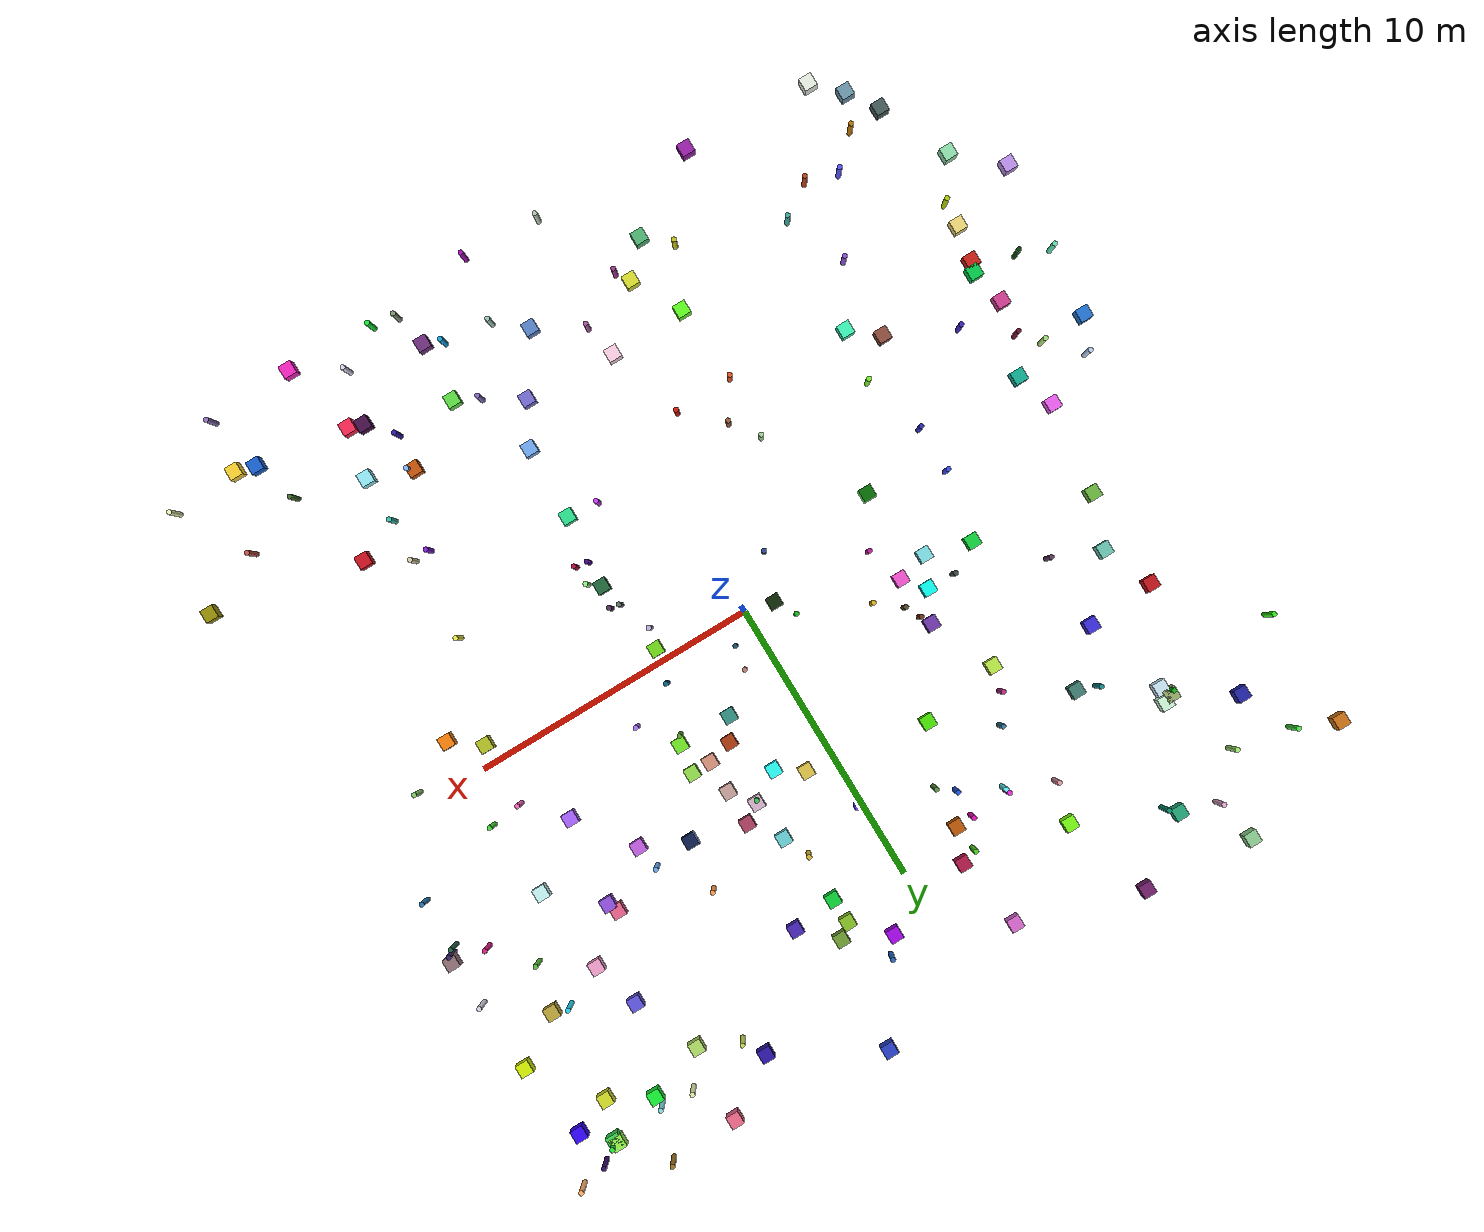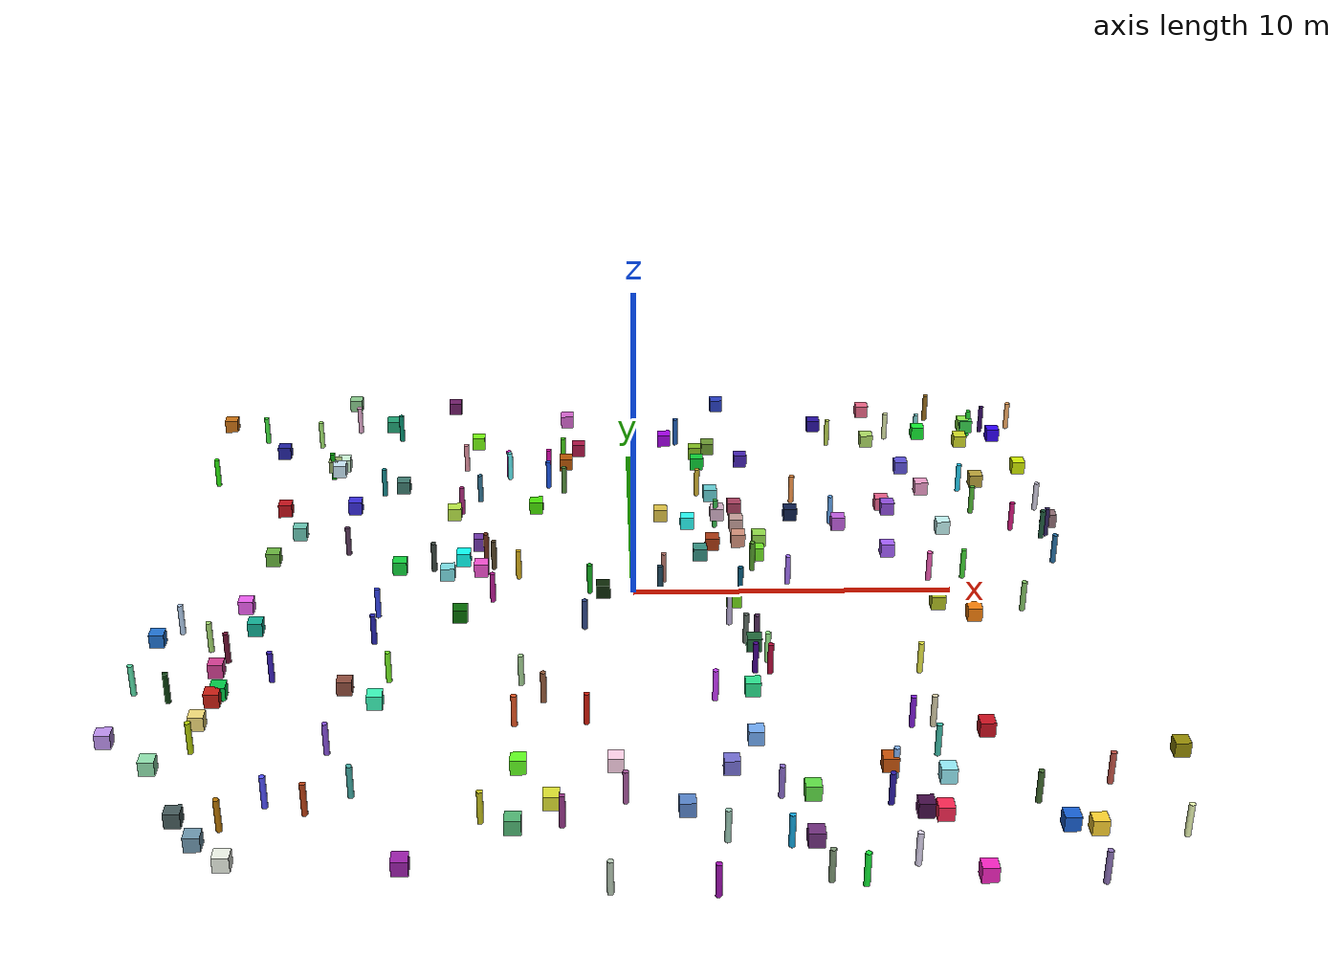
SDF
<sdf version="1.7">
 <world name="warehouse">
  <physics type="ode"><max_step_size>0.003</max_step_size><real_time_factor>1.0</real_time_factor></physics>
  <plugin name="ignition::gazebo::systems::Physics" filename="libignition-gazebo-physics-system.so"/>
  <plugin name="ignition::gazebo::systems::UserCommands" filename="libignition-gazebo-user-commands-system.so"/>
  <plugin name="ignition::gazebo::systems::SceneBroadcaster" filename="libignition-gazebo-scene-broadcaster-system.so"/>
  <plugin name="ignition::gazebo::systems::Sensors" filename="libignition-gazebo-sensors-system.so">
   <render_engine>ogre2</render_engine>
  </plugin>
  <plugin name="ignition::gazebo::systems::Imu" filename="libignition-gazebo-imu-system.so"/>
  <plugin name="ignition::gazebo::systems::NavSat" filename="libignition-gazebo-navsat-system.so"/>
  <scene>
   <ambient>1 1 1 1</ambient>
   <background>0 0 0 1</background>
   <shadows>0</shadows>
   <grid>false</grid>
  </scene>
  <spherical_coordinates>
   <surface_model>EARTH_WGS84</surface_model>
   <world_frame_orientation>ENU</world_frame_orientation>
   <latitude_deg>-22.986687</latitude_deg>
   <longitude_deg>-43.202501</longitude_deg>
   <elevation>0</elevation>
   <heading_deg>0</heading_deg>
  </spherical_coordinates>
  <model name="ground_plane">
   <static>true</static>
   <link name="link">
    <collision name="collision">
     <geometry><plane><normal>0.0 0.0 1</normal><size>1 1</size></plane></geometry>
    </collision>
   </link>
  </model>
  <model name="unit_box_0">
   <static>true</static>
   <pose>2.2 2.64 0 0 0 0</pose>
   <link name="link">
    <collision name="collision">
     <geometry><box><size>0.450000 0.450000 0.450000</size></box></geometry>
    </collision>
    <visual name="visual">
     <geometry><box><size>0.450000 0.450000 0.450000</size></box></geometry>
     <material>
      <ambient>0.2033842654098772 0.556471265459145 0.4994971915833679 1</ambient>
      <diffuse>0.2033842654098772 0.556471265459145 0.4994971915833679 1</diffuse>
      <script><uri>file://media/materials/scripts/gazebo.material</uri><name>Gazebo/RandomColor0</name></script>
     </material>
    </visual>
   </link>
  </model>
  <model name="unit_cylinder_0">
   <static>true</static>
   <pose>4.98 1.39 0 0 0 0</pose>
   <link name="link">
    <collision name="collision">
     <geometry><cylinder><radius>0.085000</radius><length>1.000000</length></cylinder></geometry>
    </collision>
    <visual name="visual">
     <geometry><cylinder><radius>0.085000</radius><length>1.000000</length></cylinder></geometry>
     <material>
      <ambient>0.6472687690180325 0.44911346281101283 0.975330917862481 1</ambient>
      <diffuse>0.6472687690180325 0.44911346281101283 0.975330917862481 1</diffuse>
      <script><uri>file://media/materials/scripts/gazebo.material</uri><name>Gazebo/RandomColor0</name></script>
     </material>
    </visual>
   </link>
  </model>
  <model name="unit_box_1">
   <static>true</static>
   <pose>-9.45 6.24 0 0 0 0</pose>
   <link name="link">
    <collision name="collision">
     <geometry><box><size>0.450000 0.450000 0.450000</size></box></geometry>
    </collision>
    <visual name="visual">
     <geometry><box><size>0.450000 0.450000 0.450000</size></box></geometry>
     <material>
      <ambient>0.22018970672033 0.168669181390797 0.8557216432038262 1</ambient>
      <diffuse>0.22018970672033 0.168669181390797 0.8557216432038262 1</diffuse>
      <script><uri>file://media/materials/scripts/gazebo.material</uri><name>Gazebo/RandomColor1</name></script>
     </material>
    </visual>
   </link>
  </model>
  <model name="unit_cylinder_1">
   <static>true</static>
   <pose>-4.3 9.48 0 0 0 0</pose>
   <link name="link">
    <collision name="collision">
     <geometry><cylinder><radius>0.085000</radius><length>1.000000</length></cylinder></geometry>
    </collision>
    <visual name="visual">
     <geometry><cylinder><radius>0.085000</radius><length>1.000000</length></cylinder></geometry>
     <material>
      <ambient>0.9275289806916635 0.16235170054518033 0.8495910540043754 1</ambient>
      <diffuse>0.9275289806916635 0.16235170054518033 0.8495910540043754 1</diffuse>
      <script><uri>file://media/materials/scripts/gazebo.material</uri><name>Gazebo/RandomColor1</name></script>
     </material>
    </visual>
   </link>
  </model>
  <model name="unit_box_2">
   <static>true</static>
   <pose>-7.58 -6.17 0 0 0 0</pose>
   <link name="link">
    <collision name="collision">
     <geometry><box><size>0.450000 0.450000 0.450000</size></box></geometry>
    </collision>
    <visual name="visual">
     <geometry><box><size>0.450000 0.450000 0.450000</size></box></geometry>
     <material>
      <ambient>0.2312825415340426 0.9723109525071806 0.7312117675803362 1</ambient>
      <diffuse>0.2312825415340426 0.9723109525071806 0.7312117675803362 1</diffuse>
      <script><uri>file://media/materials/scripts/gazebo.material</uri><name>Gazebo/RandomColor2</name></script>
     </material>
    </visual>
   </link>
  </model>
  <model name="unit_cylinder_2">
   <static>true</static>
   <pose>3.37 -2.32 0 0 0 0</pose>
   <link name="link">
    <collision name="collision">
     <geometry><cylinder><radius>0.085000</radius><length>1.000000</length></cylinder></geometry>
    </collision>
    <visual name="visual">
     <geometry><cylinder><radius>0.085000</radius><length>1.000000</length></cylinder></geometry>
     <material>
      <ambient>0.3746464560616375 0.42663091544570064 0.3947514861165152 1</ambient>
      <diffuse>0.3746464560616375 0.42663091544570064 0.3947514861165152 1</diffuse>
      <script><uri>file://media/materials/scripts/gazebo.material</uri><name>Gazebo/RandomColor2</name></script>
     </material>
    </visual>
   </link>
  </model>
  <model name="unit_box_3">
   <static>true</static>
   <pose>9.51 -0.68 0 0 0 0</pose>
   <link name="link">
    <collision name="collision">
     <geometry><box><size>0.450000 0.450000 0.450000</size></box></geometry>
    </collision>
    <visual name="visual">
     <geometry><box><size>0.450000 0.450000 0.450000</size></box></geometry>
     <material>
      <ambient>0.6892208539074204 0.7462321227307075 0.12971181196509196 1</ambient>
      <diffuse>0.6892208539074204 0.7462321227307075 0.12971181196509196 1</diffuse>
      <script><uri>file://media/materials/scripts/gazebo.material</uri><name>Gazebo/RandomColor3</name></script>
     </material>
    </visual>
   </link>
  </model>
  <model name="unit_cylinder_3">
   <static>true</static>
   <pose>7.04 -13.53 0 0 0 0</pose>
   <link name="link">
    <collision name="collision">
     <geometry><cylinder><radius>0.085000</radius><length>1.000000</length></cylinder></geometry>
    </collision>
    <visual name="visual">
     <geometry><cylinder><radius>0.085000</radius><length>1.000000</length></cylinder></geometry>
     <material>
      <ambient>0.8920071408856468 0.8596903477106197 0.968408697729801 1</ambient>
      <diffuse>0.8920071408856468 0.8596903477106197 0.968408697729801 1</diffuse>
      <script><uri>file://media/materials/scripts/gazebo.material</uri><name>Gazebo/RandomColor3</name></script>
     </material>
    </visual>
   </link>
  </model>
  <model name="unit_box_4">
   <static>true</static>
   <pose>4.58 -10.87 0 0 0 0</pose>
   <link name="link">
    <collision name="collision">
     <geometry><box><size>0.450000 0.450000 0.450000</size></box></geometry>
    </collision>
    <visual name="visual">
     <geometry><box><size>0.450000 0.450000 0.450000</size></box></geometry>
     <material>
      <ambient>0.3702599397598817 0.8748853656224929 0.27414386341138386 1</ambient>
      <diffuse>0.3702599397598817 0.8748853656224929 0.27414386341138386 1</diffuse>
      <script><uri>file://media/materials/scripts/gazebo.material</uri><name>Gazebo/RandomColor4</name></script>
     </material>
    </visual>
   </link>
  </model>
  <model name="unit_cylinder_4">
   <static>true</static>
   <pose>9.58 1.57 0 0 0 0</pose>
   <link name="link">
    <collision name="collision">
     <geometry><cylinder><radius>0.085000</radius><length>1.000000</length></cylinder></geometry>
    </collision>
    <visual name="visual">
     <geometry><cylinder><radius>0.085000</radius><length>1.000000</length></cylinder></geometry>
     <material>
      <ambient>0.9740638241613627 0.37367039531082935 0.7371137244861767 1</ambient>
      <diffuse>0.9740638241613627 0.37367039531082935 0.7371137244861767 1</diffuse>
      <script><uri>file://media/materials/scripts/gazebo.material</uri><name>Gazebo/RandomColor4</name></script>
     </material>
    </visual>
   </link>
  </model>
  <model name="unit_box_5">
   <static>true</static>
   <pose>3.97 9.73 0 0 0 0</pose>
   <link name="link">
    <collision name="collision">
     <geometry><box><size>0.450000 0.450000 0.450000</size></box></geometry>
    </collision>
    <visual name="visual">
     <geometry><box><size>0.450000 0.450000 0.450000</size></box></geometry>
     <material>
      <ambient>0.2689518017919452 0.13552714101996888 0.6945008653489603 1</ambient>
      <diffuse>0.2689518017919452 0.13552714101996888 0.6945008653489603 1</diffuse>
      <script><uri>file://media/materials/scripts/gazebo.material</uri><name>Gazebo/RandomColor5</name></script>
     </material>
    </visual>
   </link>
  </model>
  <model name="unit_cylinder_5">
   <static>true</static>
   <pose>8.46 -4.13 0 0 0 0</pose>
   <link name="link">
    <collision name="collision">
     <geometry><cylinder><radius>0.085000</radius><length>1.000000</length></cylinder></geometry>
    </collision>
    <visual name="visual">
     <geometry><cylinder><radius>0.085000</radius><length>1.000000</length></cylinder></geometry>
     <material>
      <ambient>0.9387093573292032 0.9439170657203892 0.2815634968002798 1</ambient>
      <diffuse>0.9387093573292032 0.9439170657203892 0.2815634968002798 1</diffuse>
      <script><uri>file://media/materials/scripts/gazebo.material</uri><name>Gazebo/RandomColor5</name></script>
     </material>
    </visual>
   </link>
  </model>
  <model name="unit_box_6">
   <static>true</static>
   <pose>-14.93 -8.04 0 0 0 0</pose>
   <link name="link">
    <collision name="collision">
     <geometry><box><size>0.450000 0.450000 0.450000</size></box></geometry>
    </collision>
    <visual name="visual">
     <geometry><box><size>0.450000 0.450000 0.450000</size></box></geometry>
     <material>
      <ambient>0.7430324248041168 0.5738740492089994 0.9353396482725254 1</ambient>
      <diffuse>0.7430324248041168 0.5738740492089994 0.9353396482725254 1</diffuse>
      <script><uri>file://media/materials/scripts/gazebo.material</uri><name>Gazebo/RandomColor6</name></script>
     </material>
    </visual>
   </link>
  </model>
  <model name="unit_cylinder_6">
   <static>true</static>
   <pose>14.02 4.61 0 0 0 0</pose>
   <link name="link">
    <collision name="collision">
     <geometry><cylinder><radius>0.085000</radius><length>1.000000</length></cylinder></geometry>
    </collision>
    <visual name="visual">
     <geometry><cylinder><radius>0.085000</radius><length>1.000000</length></cylinder></geometry>
     <material>
      <ambient>0.19710142438978373 0.13745172707509656 0.3912315722723817 1</ambient>
      <diffuse>0.19710142438978373 0.13745172707509656 0.3912315722723817 1</diffuse>
      <script><uri>file://media/materials/scripts/gazebo.material</uri><name>Gazebo/RandomColor6</name></script>
     </material>
    </visual>
   </link>
  </model>
  <model name="unit_box_7">
   <static>true</static>
   <pose>2.91 5.54 0 0 0 0</pose>
   <link name="link">
    <collision name="collision">
     <geometry><box><size>0.450000 0.450000 0.450000</size></box></geometry>
    </collision>
    <visual name="visual">
     <geometry><box><size>0.450000 0.450000 0.450000</size></box></geometry>
     <material>
      <ambient>0.8225502708183758 0.6867900643934398 0.7781685932627812 1</ambient>
      <diffuse>0.8225502708183758 0.6867900643934398 0.7781685932627812 1</diffuse>
      <script><uri>file://media/materials/scripts/gazebo.material</uri><name>Gazebo/RandomColor7</name></script>
     </material>
    </visual>
   </link>
  </model>
  <model name="unit_cylinder_7">
   <static>true</static>
   <pose>-1.49 -6.75 0 0 0 0</pose>
   <link name="link">
    <collision name="collision">
     <geometry><cylinder><radius>0.085000</radius><length>1.000000</length></cylinder></geometry>
    </collision>
    <visual name="visual">
     <geometry><cylinder><radius>0.085000</radius><length>1.000000</length></cylinder></geometry>
     <material>
      <ambient>0.8189590762095114 0.09994172586716332 0.036182600300354806 1</ambient>
      <diffuse>0.8189590762095114 0.09994172586716332 0.036182600300354806 1</diffuse>
      <script><uri>file://media/materials/scripts/gazebo.material</uri><name>Gazebo/RandomColor7</name></script>
     </material>
    </visual>
   </link>
  </model>
  <model name="unit_box_8">
   <static>true</static>
   <pose>-11.6 -12.82 0 0 0 0</pose>
   <link name="link">
    <collision name="collision">
     <geometry><box><size>0.450000 0.450000 0.450000</size></box></geometry>
    </collision>
    <visual name="visual">
     <geometry><box><size>0.450000 0.450000 0.450000</size></box></geometry>
     <material>
      <ambient>0.43343318827009225 0.5937559258900776 0.6828403868105664 1</ambient>
      <diffuse>0.43343318827009225 0.5937559258900776 0.6828403868105664 1</diffuse>
      <script><uri>file://media/materials/scripts/gazebo.material</uri><name>Gazebo/RandomColor8</name></script>
     </material>
    </visual>
   </link>
  </model>
  <model name="unit_cylinder_8">
   <static>true</static>
   <pose>-4.29 -11.51 0 0 0 0</pose>
   <link name="link">
    <collision name="collision">
     <geometry><cylinder><radius>0.085000</radius><length>1.000000</length></cylinder></geometry>
    </collision>
    <visual name="visual">
     <geometry><cylinder><radius>0.085000</radius><length>1.000000</length></cylinder></geometry>
     <material>
      <ambient>0.7776777248018112 0.7632080752826252 0.10930203840896058 1</ambient>
      <diffuse>0.7776777248018112 0.7632080752826252 0.10930203840896058 1</diffuse>
      <script><uri>file://media/materials/scripts/gazebo.material</uri><name>Gazebo/RandomColor8</name></script>
     </material>
    </visual>
   </link>
  </model>
  <model name="unit_box_9">
   <static>true</static>
   <pose>6.9 12.72 0 0 0 0</pose>
   <link name="link">
    <collision name="collision">
     <geometry><box><size>0.450000 0.450000 0.450000</size></box></geometry>
    </collision>
    <visual name="visual">
     <geometry><box><size>0.450000 0.450000 0.450000</size></box></geometry>
     <material>
      <ambient>0.16291486107056707 0.06930496910042805 0.6325173738668594 1</ambient>
      <diffuse>0.16291486107056707 0.06930496910042805 0.6325173738668594 1</diffuse>
      <script><uri>file://media/materials/scripts/gazebo.material</uri><name>Gazebo/RandomColor9</name></script>
     </material>
    </visual>
   </link>
  </model>
  <model name="unit_cylinder_9">
   <static>true</static>
   <pose>12.91 5.04 0 0 0 0</pose>
   <link name="link">
    <collision name="collision">
     <geometry><cylinder><radius>0.085000</radius><length>1.000000</length></cylinder></geometry>
    </collision>
    <visual name="visual">
     <geometry><cylinder><radius>0.085000</radius><length>1.000000</length></cylinder></geometry>
     <material>
      <ambient>0.8699030829575385 0.10296220234799758 0.5147589166828516 1</ambient>
      <diffuse>0.8699030829575385 0.10296220234799758 0.5147589166828516 1</diffuse>
      <script><uri>file://media/materials/scripts/gazebo.material</uri><name>Gazebo/RandomColor9</name></script>
     </material>
    </visual>
   </link>
  </model>
  <model name="unit_box_10">
   <static>true</static>
   <pose>-1.84 10.73 0 0 0 0</pose>
   <link name="link">
    <collision name="collision">
     <geometry><box><size>0.450000 0.450000 0.450000</size></box></geometry>
    </collision>
    <visual name="visual">
     <geometry><box><size>0.450000 0.450000 0.450000</size></box></geometry>
     <material>
      <ambient>0.6704528873766061 0.0826368071537057 0.27285723767520786 1</ambient>
      <diffuse>0.6704528873766061 0.0826368071537057 0.27285723767520786 1</diffuse>
      <script><uri>file://media/materials/scripts/gazebo.material</uri><name>Gazebo/RandomColor10</name></script>
     </material>
    </visual>
   </link>
  </model>
  <model name="unit_cylinder_10">
   <static>true</static>
   <pose>9.57 12.51 0 0 0 0</pose>
   <link name="link">
    <collision name="collision">
     <geometry><cylinder><radius>0.085000</radius><length>1.000000</length></cylinder></geometry>
    </collision>
    <visual name="visual">
     <geometry><cylinder><radius>0.085000</radius><length>1.000000</length></cylinder></geometry>
     <material>
      <ambient>0.885615581655553 0.9327394628002798 0.6782206357978003 1</ambient>
      <diffuse>0.885615581655553 0.9327394628002798 0.6782206357978003 1</diffuse>
      <script><uri>file://media/materials/scripts/gazebo.material</uri><name>Gazebo/RandomColor10</name></script>
     </material>
    </visual>
   </link>
  </model>
  <model name="unit_box_11">
   <static>true</static>
   <pose>-12.15 -5.6 0 0 0 0</pose>
   <link name="link">
    <collision name="collision">
     <geometry><box><size>0.450000 0.450000 0.450000</size></box></geometry>
    </collision>
    <visual name="visual">
     <geometry><box><size>0.450000 0.450000 0.450000</size></box></geometry>
     <material>
      <ambient>0.009686847005365151 0.7958886425692635 0.28912136334541993 1</ambient>
      <diffuse>0.009686847005365151 0.7958886425692635 0.28912136334541993 1</diffuse>
      <script><uri>file://media/materials/scripts/gazebo.material</uri><name>Gazebo/RandomColor11</name></script>
     </material>
    </visual>
   </link>
  </model>
  <model name="unit_cylinder_11">
   <static>true</static>
   <pose>13.84 4.43 0 0 0 0</pose>
   <link name="link">
    <collision name="collision">
     <geometry><cylinder><radius>0.085000</radius><length>1.000000</length></cylinder></geometry>
    </collision>
    <visual name="visual">
     <geometry><cylinder><radius>0.085000</radius><length>1.000000</length></cylinder></geometry>
     <material>
      <ambient>0.1335643459164848 0.3807918756871833 0.26239654531750034 1</ambient>
      <diffuse>0.1335643459164848 0.3807918756871833 0.26239654531750034 1</diffuse>
      <script><uri>file://media/materials/scripts/gazebo.material</uri><name>Gazebo/RandomColor11</name></script>
     </material>
    </visual>
   </link>
  </model>
  <model name="unit_box_12">
   <static>true</static>
   <pose>-2.42 -11.19 0 0 0 0</pose>
   <link name="link">
    <collision name="collision">
     <geometry><box><size>0.450000 0.450000 0.450000</size></box></geometry>
    </collision>
    <visual name="visual">
     <geometry><box><size>0.450000 0.450000 0.450000</size></box></geometry>
     <material>
      <ambient>0.8628598329702908 0.8815592572391001 0.18948683787233167 1</ambient>
      <diffuse>0.8628598329702908 0.8815592572391001 0.18948683787233167 1</diffuse>
      <script><uri>file://media/materials/scripts/gazebo.material</uri><name>Gazebo/RandomColor12</name></script>
     </material>
    </visual>
   </link>
  </model>
  <model name="unit_cylinder_12">
   <static>true</static>
   <pose>-5.85 10.04 0 0 0 0</pose>
   <link name="link">
    <collision name="collision">
     <geometry><cylinder><radius>0.085000</radius><length>1.000000</length></cylinder></geometry>
    </collision>
    <visual name="visual">
     <geometry><cylinder><radius>0.085000</radius><length>1.000000</length></cylinder></geometry>
     <material>
      <ambient>0.9099793979901629 0.5892522467727745 0.6506620106365731 1</ambient>
      <diffuse>0.9099793979901629 0.5892522467727745 0.6506620106365731 1</diffuse>
      <script><uri>file://media/materials/scripts/gazebo.material</uri><name>Gazebo/RandomColor12</name></script>
     </material>
    </visual>
   </link>
  </model>
  <model name="unit_box_13">
   <static>true</static>
   <pose>-12.5 -7.19 0 0 0 0</pose>
   <link name="link">
    <collision name="collision">
     <geometry><box><size>0.450000 0.450000 0.450000</size></box></geometry>
    </collision>
    <visual name="visual">
     <geometry><box><size>0.450000 0.450000 0.450000</size></box></geometry>
     <material>
      <ambient>0.9443924591899964 0.8581053386519131 0.4730509594195955 1</ambient>
      <diffuse>0.9443924591899964 0.8581053386519131 0.4730509594195955 1</diffuse>
      <script><uri>file://media/materials/scripts/gazebo.material</uri><name>Gazebo/RandomColor13</name></script>
     </material>
    </visual>
   </link>
  </model>
  <model name="unit_cylinder_13">
   <static>true</static>
   <pose>-4.82 3.12 0 0 0 0</pose>
   <link name="link">
    <collision name="collision">
     <geometry><cylinder><radius>0.085000</radius><length>1.000000</length></cylinder></geometry>
    </collision>
    <visual name="visual">
     <geometry><cylinder><radius>0.085000</radius><length>1.000000</length></cylinder></geometry>
     <material>
      <ambient>0.44348084139480304 0.1950857366091988 0.1112470507666955 1</ambient>
      <diffuse>0.44348084139480304 0.1950857366091988 0.1112470507666955 1</diffuse>
      <script><uri>file://media/materials/scripts/gazebo.material</uri><name>Gazebo/RandomColor13</name></script>
     </material>
    </visual>
   </link>
  </model>
  <model name="unit_box_14">
   <static>true</static>
   <pose>6.96 4.77 0 0 0 0</pose>
   <link name="link">
    <collision name="collision">
     <geometry><box><size>0.450000 0.450000 0.450000</size></box></geometry>
    </collision>
    <visual name="visual">
     <geometry><box><size>0.450000 0.450000 0.450000</size></box></geometry>
     <material>
      <ambient>0.7507526792527157 0.36376964360259534 0.8690091851841476 1</ambient>
      <diffuse>0.7507526792527157 0.36376964360259534 0.8690091851841476 1</diffuse>
      <script><uri>file://media/materials/scripts/gazebo.material</uri><name>Gazebo/RandomColor14</name></script>
     </material>
    </visual>
   </link>
  </model>
  <model name="unit_cylinder_14">
   <static>true</static>
   <pose>6.97 -9.67 0 0 0 0</pose>
   <link name="link">
    <collision name="collision">
     <geometry><cylinder><radius>0.085000</radius><length>1.000000</length></cylinder></geometry>
    </collision>
    <visual name="visual">
     <geometry><cylinder><radius>0.085000</radius><length>1.000000</length></cylinder></geometry>
     <material>
      <ambient>0.5327696640421138 0.7274066079611091 0.9815210943056651 1</ambient>
      <diffuse>0.5327696640421138 0.7274066079611091 0.9815210943056651 1</diffuse>
      <script><uri>file://media/materials/scripts/gazebo.material</uri><name>Gazebo/RandomColor14</name></script>
     </material>
    </visual>
   </link>
  </model>
  <model name="unit_box_15">
   <static>true</static>
   <pose>-11.63 -1.93 0 0 0 0</pose>
   <link name="link">
    <collision name="collision">
     <geometry><box><size>0.450000 0.450000 0.450000</size></box></geometry>
    </collision>
    <visual name="visual">
     <geometry><box><size>0.450000 0.450000 0.450000</size></box></geometry>
     <material>
      <ambient>0.06534427168459656 0.6835050197864069 0.5798323271976961 1</ambient>
      <diffuse>0.06534427168459656 0.6835050197864069 0.5798323271976961 1</diffuse>
      <script><uri>file://media/materials/scripts/gazebo.material</uri><name>Gazebo/RandomColor15</name></script>
     </material>
    </visual>
   </link>
  </model>
  <model name="unit_cylinder_15">
   <static>true</static>
   <pose>-8.75 -8.18 0 0 0 0</pose>
   <link name="link">
    <collision name="collision">
     <geometry><cylinder><radius>0.085000</radius><length>1.000000</length></cylinder></geometry>
    </collision>
    <visual name="visual">
     <geometry><cylinder><radius>0.085000</radius><length>1.000000</length></cylinder></geometry>
     <material>
      <ambient>0.530437266507116 0.3187241931810576 0.8595011456076574 1</ambient>
      <diffuse>0.530437266507116 0.3187241931810576 0.8595011456076574 1</diffuse>
      <script><uri>file://media/materials/scripts/gazebo.material</uri><name>Gazebo/RandomColor15</name></script>
     </material>
    </visual>
   </link>
  </model>
  <model name="unit_box_16">
   <static>true</static>
   <pose>-11.82 6.08 0 0 0 0</pose>
   <link name="link">
    <collision name="collision">
     <geometry><box><size>0.450000 0.450000 0.450000</size></box></geometry>
    </collision>
    <visual name="visual">
     <geometry><box><size>0.450000 0.450000 0.450000</size></box></geometry>
     <material>
      <ambient>0.7576021204140397 0.06908343477428247 0.1029401630925113 1</ambient>
      <diffuse>0.7576021204140397 0.06908343477428247 0.1029401630925113 1</diffuse>
      <script><uri>file://media/materials/scripts/gazebo.material</uri><name>Gazebo/RandomColor16</name></script>
     </material>
    </visual>
   </link>
  </model>
  <model name="unit_cylinder_16">
   <static>true</static>
   <pose>2.94 -1.17 0 0 0 0</pose>
   <link name="link">
    <collision name="collision">
     <geometry><cylinder><radius>0.085000</radius><length>1.000000</length></cylinder></geometry>
    </collision>
    <visual name="visual">
     <geometry><cylinder><radius>0.085000</radius><length>1.000000</length></cylinder></geometry>
     <material>
      <ambient>0.7558042645364538 0.7023735235230681 0.8694856708727956 1</ambient>
      <diffuse>0.7558042645364538 0.7023735235230681 0.8694856708727956 1</diffuse>
      <script><uri>file://media/materials/scripts/gazebo.material</uri><name>Gazebo/RandomColor16</name></script>
     </material>
    </visual>
   </link>
  </model>
  <model name="unit_box_17">
   <static>true</static>
   <pose>-10.33 14.91 0 0 0 0</pose>
   <link name="link">
    <collision name="collision">
     <geometry><box><size>0.450000 0.450000 0.450000</size></box></geometry>
    </collision>
    <visual name="visual">
     <geometry><box><size>0.450000 0.450000 0.450000</size></box></geometry>
     <material>
      <ambient>0.5380822836888527 0.7951779781985044 0.5547439271741642 1</ambient>
      <diffuse>0.5380822836888527 0.7951779781985044 0.5547439271741642 1</diffuse>
      <script><uri>file://media/materials/scripts/gazebo.material</uri><name>Gazebo/RandomColor17</name></script>
     </material>
    </visual>
   </link>
  </model>
  <model name="unit_cylinder_17">
   <static>true</static>
   <pose>3.4 0.67 0 0 0 0</pose>
   <link name="link">
    <collision name="collision">
     <geometry><cylinder><radius>0.085000</radius><length>1.000000</length></cylinder></geometry>
    </collision>
    <visual name="visual">
     <geometry><cylinder><radius>0.085000</radius><length>1.000000</length></cylinder></geometry>
     <material>
      <ambient>0.025559428308082666 0.37222367877323703 0.513266187301278 1</ambient>
      <diffuse>0.025559428308082666 0.37222367877323703 0.513266187301278 1</diffuse>
      <script><uri>file://media/materials/scripts/gazebo.material</uri><name>Gazebo/RandomColor17</name></script>
     </material>
    </visual>
   </link>
  </model>
  <model name="unit_box_18">
   <static>true</static>
   <pose>1.29 11.55 0 0 0 0</pose>
   <link name="link">
    <collision name="collision">
     <geometry><box><size>0.450000 0.450000 0.450000</size></box></geometry>
    </collision>
    <visual name="visual">
     <geometry><box><size>0.450000 0.450000 0.450000</size></box></geometry>
     <material>
      <ambient>0.6316145346749856 0.011948659295485164 0.8916331385772003 1</ambient>
      <diffuse>0.6316145346749856 0.011948659295485164 0.8916331385772003 1</diffuse>
      <script><uri>file://media/materials/scripts/gazebo.material</uri><name>Gazebo/RandomColor18</name></script>
     </material>
    </visual>
   </link>
  </model>
  <model name="unit_cylinder_18">
   <static>true</static>
   <pose>14.3 13.37 0 0 0 0</pose>
   <link name="link">
    <collision name="collision">
     <geometry><cylinder><radius>0.085000</radius><length>1.000000</length></cylinder></geometry>
    </collision>
    <visual name="visual">
     <geometry><cylinder><radius>0.085000</radius><length>1.000000</length></cylinder></geometry>
     <material>
      <ambient>0.9898269840798938 0.6891691866875646 0.4007298907136404 1</ambient>
      <diffuse>0.9898269840798938 0.6891691866875646 0.4007298907136404 1</diffuse>
      <script><uri>file://media/materials/scripts/gazebo.material</uri><name>Gazebo/RandomColor18</name></script>
     </material>
    </visual>
   </link>
  </model>
  <model name="unit_box_19">
   <static>true</static>
   <pose>-2.27 9.59 0 0 0 0</pose>
   <link name="link">
    <collision name="collision">
     <geometry><box><size>0.450000 0.450000 0.450000</size></box></geometry>
    </collision>
    <visual name="visual">
     <geometry><box><size>0.450000 0.450000 0.450000</size></box></geometry>
     <material>
      <ambient>0.7203460917915703 0.333728805976085 0.017275516002810187 1</ambient>
      <diffuse>0.7203460917915703 0.333728805976085 0.017275516002810187 1</diffuse>
      <script><uri>file://media/materials/scripts/gazebo.material</uri><name>Gazebo/RandomColor19</name></script>
     </material>
    </visual>
   </link>
  </model>
  <model name="unit_cylinder_19">
   <static>true</static>
   <pose>7.35 11.98 0 0 0 0</pose>
   <link name="link">
    <collision name="collision">
     <geometry><cylinder><radius>0.085000</radius><length>1.000000</length></cylinder></geometry>
    </collision>
    <visual name="visual">
     <geometry><cylinder><radius>0.085000</radius><length>1.000000</length></cylinder></geometry>
     <material>
      <ambient>0.7488498056593774 0.8509600717235335 0.31902658749661494 1</ambient>
      <diffuse>0.7488498056593774 0.8509600717235335 0.31902658749661494 1</diffuse>
      <script><uri>file://media/materials/scripts/gazebo.material</uri><name>Gazebo/RandomColor19</name></script>
     </material>
    </visual>
   </link>
  </model>
  <model name="unit_box_20">
   <static>true</static>
   <pose>12.53 12.68 0 0 0 0</pose>
   <link name="link">
    <collision name="collision">
     <geometry><box><size>0.450000 0.450000 0.450000</size></box></geometry>
    </collision>
    <visual name="visual">
     <geometry><box><size>0.450000 0.450000 0.450000</size></box></geometry>
     <material>
      <ambient>0.5615916827636068 0.9328652311126638 0.28886881989030055 1</ambient>
      <diffuse>0.5615916827636068 0.9328652311126638 0.28886881989030055 1</diffuse>
      <script><uri>file://media/materials/scripts/gazebo.material</uri><name>Gazebo/RandomColor20</name></script>
     </material>
    </visual>
   </link>
  </model>
  <model name="unit_cylinder_20">
   <static>true</static>
   <pose>11.7 -14.37 0 0 0 0</pose>
   <link name="link">
    <collision name="collision">
     <geometry><cylinder><radius>0.085000</radius><length>1.000000</length></cylinder></geometry>
    </collision>
    <visual name="visual">
     <geometry><cylinder><radius>0.085000</radius><length>1.000000</length></cylinder></geometry>
     <material>
      <ambient>0.559423304301949 0.452603501856227 0.7339535909351613 1</ambient>
      <diffuse>0.559423304301949 0.452603501856227 0.7339535909351613 1</diffuse>
      <script><uri>file://media/materials/scripts/gazebo.material</uri><name>Gazebo/RandomColor20</name></script>
     </material>
    </visual>
   </link>
  </model>
  <model name="unit_box_21">
   <static>true</static>
   <pose>8.38 2.82 0 0 0 0</pose>
   <link name="link">
    <collision name="collision">
     <geometry><box><size>0.450000 0.450000 0.450000</size></box></geometry>
    </collision>
    <visual name="visual">
     <geometry><box><size>0.450000 0.450000 0.450000</size></box></geometry>
     <material>
      <ambient>0.648935899689679 0.38077725477574254 0.9904537576113294 1</ambient>
      <diffuse>0.648935899689679 0.38077725477574254 0.9904537576113294 1</diffuse>
      <script><uri>file://media/materials/scripts/gazebo.material</uri><name>Gazebo/RandomColor21</name></script>
     </material>
    </visual>
   </link>
  </model>
  <model name="unit_cylinder_21">
   <static>true</static>
   <pose>-1.41 0.93 0 0 0 0</pose>
   <link name="link">
    <collision name="collision">
     <geometry><cylinder><radius>0.085000</radius><length>1.000000</length></cylinder></geometry>
    </collision>
    <visual name="visual">
     <geometry><cylinder><radius>0.085000</radius><length>1.000000</length></cylinder></geometry>
     <material>
      <ambient>0.07495171647082388 0.7108869150053795 0.1288022748435972 1</ambient>
      <diffuse>0.07495171647082388 0.7108869150053795 0.1288022748435972 1</diffuse>
      <script><uri>file://media/materials/scripts/gazebo.material</uri><name>Gazebo/RandomColor21</name></script>
     </material>
    </visual>
   </link>
  </model>
  <model name="unit_box_22">
   <static>true</static>
   <pose>-11.73 2.57 0 0 0 0</pose>
   <link name="link">
    <collision name="collision">
     <geometry><box><size>0.450000 0.450000 0.450000</size></box></geometry>
    </collision>
    <visual name="visual">
     <geometry><box><size>0.450000 0.450000 0.450000</size></box></geometry>
     <material>
      <ambient>0.41077580032912864 0.7096107871756682 0.2456619725342214 1</ambient>
      <diffuse>0.41077580032912864 0.7096107871756682 0.2456619725342214 1</diffuse>
      <script><uri>file://media/materials/scripts/gazebo.material</uri><name>Gazebo/RandomColor22</name></script>
     </material>
    </visual>
   </link>
  </model>
  <model name="unit_cylinder_22">
   <static>true</static>
   <pose>3.86 -12.69 0 0 0 0</pose>
   <link name="link">
    <collision name="collision">
     <geometry><cylinder><radius>0.085000</radius><length>1.000000</length></cylinder></geometry>
    </collision>
    <visual name="visual">
     <geometry><cylinder><radius>0.085000</radius><length>1.000000</length></cylinder></geometry>
     <material>
      <ambient>0.07566895835759424 0.658932597697532 0.8795636646239717 1</ambient>
      <diffuse>0.07566895835759424 0.658932597697532 0.8795636646239717 1</diffuse>
      <script><uri>file://media/materials/scripts/gazebo.material</uri><name>Gazebo/RandomColor22</name></script>
     </material>
    </visual>
   </link>
  </model>
  <model name="unit_box_23">
   <static>true</static>
   <pose>8.77 5.85 0 0 0 0</pose>
   <link name="link">
    <collision name="collision">
     <geometry><box><size>0.450000 0.450000 0.450000</size></box></geometry>
    </collision>
    <visual name="visual">
     <geometry><box><size>0.450000 0.450000 0.450000</size></box></geometry>
     <material>
      <ambient>0.5628232391834205 0.30659823636977745 0.8610150208894195 1</ambient>
      <diffuse>0.5628232391834205 0.30659823636977745 0.8610150208894195 1</diffuse>
      <script><uri>file://media/materials/scripts/gazebo.material</uri><name>Gazebo/RandomColor23</name></script>
     </material>
    </visual>
   </link>
  </model>
  <model name="unit_cylinder_23">
   <static>true</static>
   <pose>-8.42 12.65 0 0 0 0</pose>
   <link name="link">
    <collision name="collision">
     <geometry><cylinder><radius>0.085000</radius><length>1.000000</length></cylinder></geometry>
    </collision>
    <visual name="visual">
     <geometry><cylinder><radius>0.085000</radius><length>1.000000</length></cylinder></geometry>
     <material>
      <ambient>0.023712384570412137 0.5786982690521715 0.4533886815752537 1</ambient>
      <diffuse>0.023712384570412137 0.5786982690521715 0.4533886815752537 1</diffuse>
      <script><uri>file://media/materials/scripts/gazebo.material</uri><name>Gazebo/RandomColor23</name></script>
     </material>
    </visual>
   </link>
  </model>
  <model name="unit_box_24">
   <static>true</static>
   <pose>-3.35 -9.5 0 0 0 0</pose>
   <link name="link">
    <collision name="collision">
     <geometry><box><size>0.450000 0.450000 0.450000</size></box></geometry>
    </collision>
    <visual name="visual">
     <geometry><box><size>0.450000 0.450000 0.450000</size></box></geometry>
     <material>
      <ambient>0.3853448783392829 0.9978339342402089 0.13066771843222946 1</ambient>
      <diffuse>0.3853448783392829 0.9978339342402089 0.13066771843222946 1</diffuse>
      <script><uri>file://media/materials/scripts/gazebo.material</uri><name>Gazebo/RandomColor24</name></script>
     </material>
    </visual>
   </link>
  </model>
  <model name="unit_cylinder_24">
   <static>true</static>
   <pose>-3.56 -6.82 0 0 0 0</pose>
   <link name="link">
    <collision name="collision">
     <geometry><cylinder><radius>0.085000</radius><length>1.000000</length></cylinder></geometry>
    </collision>
    <visual name="visual">
     <geometry><cylinder><radius>0.085000</radius><length>1.000000</length></cylinder></geometry>
     <material>
      <ambient>0.8979513443236309 0.3369754812882023 0.14180600407933364 1</ambient>
      <diffuse>0.8979513443236309 0.3369754812882023 0.14180600407933364 1</diffuse>
      <script><uri>file://media/materials/scripts/gazebo.material</uri><name>Gazebo/RandomColor24</name></script>
     </material>
    </visual>
   </link>
  </model>
  <model name="unit_box_25">
   <static>true</static>
   <pose>3.56 -3.14 0 0 0 0</pose>
   <link name="link">
    <collision name="collision">
     <geometry><box><size>0.450000 0.450000 0.450000</size></box></geometry>
    </collision>
    <visual name="visual">
     <geometry><box><size>0.450000 0.450000 0.450000</size></box></geometry>
     <material>
      <ambient>0.12723923879833288 0.40651373765488397 0.22832273969857164 1</ambient>
      <diffuse>0.12723923879833288 0.40651373765488397 0.22832273969857164 1</diffuse>
      <script><uri>file://media/materials/scripts/gazebo.material</uri><name>Gazebo/RandomColor25</name></script>
     </material>
    </visual>
   </link>
  </model>
  <model name="unit_cylinder_25">
   <static>true</static>
   <pose>11.33 14.17 0 0 0 0</pose>
   <link name="link">
    <collision name="collision">
     <geometry><cylinder><radius>0.085000</radius><length>1.000000</length></cylinder></geometry>
    </collision>
    <visual name="visual">
     <geometry><cylinder><radius>0.085000</radius><length>1.000000</length></cylinder></geometry>
     <material>
      <ambient>0.6116783902328166 0.43683361299034196 0.11901116937625511 1</ambient>
      <diffuse>0.6116783902328166 0.43683361299034196 0.11901116937625511 1</diffuse>
      <script><uri>file://media/materials/scripts/gazebo.material</uri><name>Gazebo/RandomColor25</name></script>
     </material>
    </visual>
   </link>
  </model>
  <model name="unit_box_26">
   <static>true</static>
   <pose>10.16 7.41 0 0 0 0</pose>
   <link name="link">
    <collision name="collision">
     <geometry><box><size>0.450000 0.450000 0.450000</size></box></geometry>
    </collision>
    <visual name="visual">
     <geometry><box><size>0.450000 0.450000 0.450000</size></box></geometry>
     <material>
      <ambient>0.9336419476547954 0.6104796904993816 0.7869507851211449 1</ambient>
      <diffuse>0.9336419476547954 0.6104796904993816 0.7869507851211449 1</diffuse>
      <script><uri>file://media/materials/scripts/gazebo.material</uri><name>Gazebo/RandomColor26</name></script>
     </material>
    </visual>
   </link>
  </model>
  <model name="unit_cylinder_26">
   <static>true</static>
   <pose>-6.5 2.48 0 0 0 0</pose>
   <link name="link">
    <collision name="collision">
     <geometry><cylinder><radius>0.085000</radius><length>1.000000</length></cylinder></geometry>
    </collision>
    <visual name="visual">
     <geometry><cylinder><radius>0.085000</radius><length>1.000000</length></cylinder></geometry>
     <material>
      <ambient>0.2324987072521133 0.27767684038715057 0.25354537623528006 1</ambient>
      <diffuse>0.2324987072521133 0.27767684038715057 0.25354537623528006 1</diffuse>
      <script><uri>file://media/materials/scripts/gazebo.material</uri><name>Gazebo/RandomColor26</name></script>
     </material>
    </visual>
   </link>
  </model>
  <model name="unit_box_27">
   <static>true</static>
   <pose>-4.91 1.72 0 0 0 0</pose>
   <link name="link">
    <collision name="collision">
     <geometry><box><size>0.450000 0.450000 0.450000</size></box></geometry>
    </collision>
    <visual name="visual">
     <geometry><box><size>0.450000 0.450000 0.450000</size></box></geometry>
     <material>
      <ambient>0.9500780299035041 0.3202009594664772 0.8172003858229484 1</ambient>
      <diffuse>0.9500780299035041 0.3202009594664772 0.8172003858229484 1</diffuse>
      <script><uri>file://media/materials/scripts/gazebo.material</uri><name>Gazebo/RandomColor27</name></script>
     </material>
    </visual>
   </link>
  </model>
  <model name="unit_cylinder_27">
   <static>true</static>
   <pose>-8.99 -11.06 0 0 0 0</pose>
   <link name="link">
    <collision name="collision">
     <geometry><cylinder><radius>0.085000</radius><length>1.000000</length></cylinder></geometry>
    </collision>
    <visual name="visual">
     <geometry><cylinder><radius>0.085000</radius><length>1.000000</length></cylinder></geometry>
     <material>
      <ambient>0.7366144922866806 0.25773160699544395 0.08786610210633872 1</ambient>
      <diffuse>0.7366144922866806 0.25773160699544395 0.08786610210633872 1</diffuse>
      <script><uri>file://media/materials/scripts/gazebo.material</uri><name>Gazebo/RandomColor27</name></script>
     </material>
    </visual>
   </link>
  </model>
  <model name="unit_box_28">
   <static>true</static>
   <pose>-10.71 -13.7 0 0 0 0</pose>
   <link name="link">
    <collision name="collision">
     <geometry><box><size>0.450000 0.450000 0.450000</size></box></geometry>
    </collision>
    <visual name="visual">
     <geometry><box><size>0.450000 0.450000 0.450000</size></box></geometry>
     <material>
      <ambient>0.9300580041193878 0.9546250954297362 0.910626091757256 1</ambient>
      <diffuse>0.9300580041193878 0.9546250954297362 0.910626091757256 1</diffuse>
      <script><uri>file://media/materials/scripts/gazebo.material</uri><name>Gazebo/RandomColor28</name></script>
     </material>
    </visual>
   </link>
  </model>
  <model name="unit_cylinder_28">
   <static>true</static>
   <pose>2.34 7.89 0 0 0 0</pose>
   <link name="link">
    <collision name="collision">
     <geometry><cylinder><radius>0.085000</radius><length>1.000000</length></cylinder></geometry>
    </collision>
    <visual name="visual">
     <geometry><cylinder><radius>0.085000</radius><length>1.000000</length></cylinder></geometry>
     <material>
      <ambient>0.8413486732190769 0.7128975307603295 0.19394356529379342 1</ambient>
      <diffuse>0.8413486732190769 0.7128975307603295 0.19394356529379342 1</diffuse>
      <script><uri>file://media/materials/scripts/gazebo.material</uri><name>Gazebo/RandomColor28</name></script>
     </material>
    </visual>
   </link>
  </model>
  <model name="unit_box_29">
   <static>true</static>
   <pose>5.4 5.48 0 0 0 0</pose>
   <link name="link">
    <collision name="collision">
     <geometry><box><size>0.450000 0.450000 0.450000</size></box></geometry>
    </collision>
    <visual name="visual">
     <geometry><box><size>0.450000 0.450000 0.450000</size></box></geometry>
     <material>
      <ambient>0.05638987536805984 0.11969565435877527 0.29882511601250117 1</ambient>
      <diffuse>0.05638987536805984 0.11969565435877527 0.29882511601250117 1</diffuse>
      <script><uri>file://media/materials/scripts/gazebo.material</uri><name>Gazebo/RandomColor29</name></script>
     </material>
    </visual>
   </link>
  </model>
  <model name="unit_cylinder_29">
   <static>true</static>
   <pose>14.28 -12.43 0 0 0 0</pose>
   <link name="link">
    <collision name="collision">
     <geometry><cylinder><radius>0.085000</radius><length>1.000000</length></cylinder></geometry>
    </collision>
    <visual name="visual">
     <geometry><cylinder><radius>0.085000</radius><length>1.000000</length></cylinder></geometry>
     <material>
      <ambient>0.9449069678931269 0.9978542921727368 0.7190663589255396 1</ambient>
      <diffuse>0.9449069678931269 0.9978542921727368 0.7190663589255396 1</diffuse>
      <script><uri>file://media/materials/scripts/gazebo.material</uri><name>Gazebo/RandomColor29</name></script>
     </material>
    </visual>
   </link>
  </model>
  <model name="unit_box_30">
   <static>true</static>
   <pose>-6.02 5.71 0 0 0 0</pose>
   <link name="link">
    <collision name="collision">
     <geometry><box><size>0.450000 0.450000 0.450000</size></box></geometry>
    </collision>
    <visual name="visual">
     <geometry><box><size>0.450000 0.450000 0.450000</size></box></geometry>
     <material>
      <ambient>0.7271689009559735 0.9087428725407991 0.273622600146868 1</ambient>
      <diffuse>0.7271689009559735 0.9087428725407991 0.273622600146868 1</diffuse>
      <script><uri>file://media/materials/scripts/gazebo.material</uri><name>Gazebo/RandomColor30</name></script>
     </material>
    </visual>
   </link>
  </model>
  <model name="unit_cylinder_30">
   <static>true</static>
   <pose>-2.38 10.54 0 0 0 0</pose>
   <link name="link">
    <collision name="collision">
     <geometry><cylinder><radius>0.085000</radius><length>1.000000</length></cylinder></geometry>
    </collision>
    <visual name="visual">
     <geometry><cylinder><radius>0.085000</radius><length>1.000000</length></cylinder></geometry>
     <material>
      <ambient>0.2739373292414402 0.8210564618751169 0.09941739432389352 1</ambient>
      <diffuse>0.2739373292414402 0.8210564618751169 0.09941739432389352 1</diffuse>
      <script><uri>file://media/materials/scripts/gazebo.material</uri><name>Gazebo/RandomColor30</name></script>
     </material>
    </visual>
   </link>
  </model>
  <model name="unit_box_31">
   <static>true</static>
   <pose>7.97 -11.87 0 0 0 0</pose>
   <link name="link">
    <collision name="collision">
     <geometry><box><size>0.450000 0.450000 0.450000</size></box></geometry>
    </collision>
    <visual name="visual">
     <geometry><box><size>0.450000 0.450000 0.450000</size></box></geometry>
     <material>
      <ambient>0.9739263839673344 0.15357265241731488 0.3225862336685429 1</ambient>
      <diffuse>0.9739263839673344 0.15357265241731488 0.3225862336685429 1</diffuse>
      <script><uri>file://media/materials/scripts/gazebo.material</uri><name>Gazebo/RandomColor31</name></script>
     </material>
    </visual>
   </link>
  </model>
  <model name="unit_cylinder_31">
   <static>true</static>
   <pose>12.81 -10.0 0 0 0 0</pose>
   <link name="link">
    <collision name="collision">
     <geometry><cylinder><radius>0.085000</radius><length>1.000000</length></cylinder></geometry>
    </collision>
    <visual name="visual">
     <geometry><cylinder><radius>0.085000</radius><length>1.000000</length></cylinder></geometry>
     <material>
      <ambient>0.7773817020315099 0.3339801391378936 0.2866794821118821 1</ambient>
      <diffuse>0.7773817020315099 0.3339801391378936 0.2866794821118821 1</diffuse>
      <script><uri>file://media/materials/scripts/gazebo.material</uri><name>Gazebo/RandomColor31</name></script>
     </material>
    </visual>
   </link>
  </model>
  <model name="unit_box_32">
   <static>true</static>
   <pose>11.88 -12.56 0 0 0 0</pose>
   <link name="link">
    <collision name="collision">
     <geometry><box><size>0.450000 0.450000 0.450000</size></box></geometry>
    </collision>
    <visual name="visual">
     <geometry><box><size>0.450000 0.450000 0.450000</size></box></geometry>
     <material>
      <ambient>0.9889561515364196 0.8230954139467405 0.19053512791781424 1</ambient>
      <diffuse>0.9889561515364196 0.8230954139467405 0.19053512791781424 1</diffuse>
      <script><uri>file://media/materials/scripts/gazebo.material</uri><name>Gazebo/RandomColor32</name></script>
     </material>
    </visual>
   </link>
  </model>
  <model name="unit_cylinder_32">
   <static>true</static>
   <pose>-2.88 8.6 0 0 0 0</pose>
   <link name="link">
    <collision name="collision">
     <geometry><cylinder><radius>0.085000</radius><length>1.000000</length></cylinder></geometry>
    </collision>
    <visual name="visual">
     <geometry><cylinder><radius>0.085000</radius><length>1.000000</length></cylinder></geometry>
     <material>
      <ambient>0.10574626899484596 0.3377778595444839 0.9206881930309955 1</ambient>
      <diffuse>0.10574626899484596 0.3377778595444839 0.9206881930309955 1</diffuse>
      <script><uri>file://media/materials/scripts/gazebo.material</uri><name>Gazebo/RandomColor32</name></script>
     </material>
    </visual>
   </link>
  </model>
  <model name="unit_box_33">
   <static>true</static>
   <pose>8.87 14.02 0 0 0 0</pose>
   <link name="link">
    <collision name="collision">
     <geometry><box><size>0.450000 0.450000 0.450000</size></box></geometry>
    </collision>
    <visual name="visual">
     <geometry><box><size>0.450000 0.450000 0.450000</size></box></geometry>
     <material>
      <ambient>0.9151545859385455 0.3940071737118407 0.5230690205111004 1</ambient>
      <diffuse>0.9151545859385455 0.3940071737118407 0.5230690205111004 1</diffuse>
      <script><uri>file://media/materials/scripts/gazebo.material</uri><name>Gazebo/RandomColor33</name></script>
     </material>
    </visual>
   </link>
  </model>
  <model name="unit_cylinder_33">
   <static>true</static>
   <pose>-5.82 6.57 0 0 0 0</pose>
   <link name="link">
    <collision name="collision">
     <geometry><cylinder><radius>0.085000</radius><length>1.000000</length></cylinder></geometry>
    </collision>
    <visual name="visual">
     <geometry><cylinder><radius>0.085000</radius><length>1.000000</length></cylinder></geometry>
     <material>
      <ambient>0.7002240023368198 0.1709598156662433 0.5054125950649161 1</ambient>
      <diffuse>0.7002240023368198 0.1709598156662433 0.5054125950649161 1</diffuse>
      <script><uri>file://media/materials/scripts/gazebo.material</uri><name>Gazebo/RandomColor33</name></script>
     </material>
    </visual>
   </link>
  </model>
  <model name="unit_box_34">
   <static>true</static>
   <pose>3.52 5.96 0 0 0 0</pose>
   <link name="link">
    <collision name="collision">
     <geometry><box><size>0.450000 0.450000 0.450000</size></box></geometry>
    </collision>
    <visual name="visual">
     <geometry><box><size>0.450000 0.450000 0.450000</size></box></geometry>
     <material>
      <ambient>0.6561970062668703 0.23972032183856584 0.36868919088388585 1</ambient>
      <diffuse>0.6561970062668703 0.23972032183856584 0.36868919088388585 1</diffuse>
      <script><uri>file://media/materials/scripts/gazebo.material</uri><name>Gazebo/RandomColor34</name></script>
     </material>
    </visual>
   </link>
  </model>
  <model name="unit_cylinder_34">
   <static>true</static>
   <pose>-13.69 -5.43 0 0 0 0</pose>
   <link name="link">
    <collision name="collision">
     <geometry><cylinder><radius>0.085000</radius><length>1.000000</length></cylinder></geometry>
    </collision>
    <visual name="visual">
     <geometry><cylinder><radius>0.085000</radius><length>1.000000</length></cylinder></geometry>
     <material>
      <ambient>0.03460307237287197 0.22997860080729615 0.04798962728053702 1</ambient>
      <diffuse>0.03460307237287197 0.22997860080729615 0.04798962728053702 1</diffuse>
      <script><uri>file://media/materials/scripts/gazebo.material</uri><name>Gazebo/RandomColor34</name></script>
     </material>
    </visual>
   </link>
  </model>
  <model name="unit_box_35">
   <static>true</static>
   <pose>7.48 -11.7 0 0 0 0</pose>
   <link name="link">
    <collision name="collision">
     <geometry><box><size>0.450000 0.450000 0.450000</size></box></geometry>
    </collision>
    <visual name="visual">
     <geometry><box><size>0.450000 0.450000 0.450000</size></box></geometry>
     <material>
      <ambient>0.26925403802783665 0.05446949683767777 0.28263844582294484 1</ambient>
      <diffuse>0.26925403802783665 0.05446949683767777 0.28263844582294484 1</diffuse>
      <script><uri>file://media/materials/scripts/gazebo.material</uri><name>Gazebo/RandomColor35</name></script>
     </material>
    </visual>
   </link>
  </model>
  <model name="unit_cylinder_35">
   <static>true</static>
   <pose>14.04 6.55 0 0 0 0</pose>
   <link name="link">
    <collision name="collision">
     <geometry><cylinder><radius>0.085000</radius><length>1.000000</length></cylinder></geometry>
    </collision>
    <visual name="visual">
     <geometry><cylinder><radius>0.085000</radius><length>1.000000</length></cylinder></geometry>
     <material>
      <ambient>0.8516509255849015 0.8344352301881542 0.9122549387257622 1</ambient>
      <diffuse>0.8516509255849015 0.8344352301881542 0.9122549387257622 1</diffuse>
      <script><uri>file://media/materials/scripts/gazebo.material</uri><name>Gazebo/RandomColor35</name></script>
     </material>
    </visual>
   </link>
  </model>
  <model name="unit_box_36">
   <static>true</static>
   <pose>-3.4 -12.25 0 0 0 0</pose>
   <link name="link">
    <collision name="collision">
     <geometry><box><size>0.450000 0.450000 0.450000</size></box></geometry>
    </collision>
    <visual name="visual">
     <geometry><box><size>0.450000 0.450000 0.450000</size></box></geometry>
     <material>
      <ambient>0.31275270385400844 0.7114897631354671 0.4526394075071719 1</ambient>
      <diffuse>0.31275270385400844 0.7114897631354671 0.4526394075071719 1</diffuse>
      <script><uri>file://media/materials/scripts/gazebo.material</uri><name>Gazebo/RandomColor36</name></script>
     </material>
    </visual>
   </link>
  </model>
  <model name="unit_cylinder_36">
   <static>true</static>
   <pose>1.84 -14.73 0 0 0 0</pose>
   <link name="link">
    <collision name="collision">
     <geometry><cylinder><radius>0.085000</radius><length>1.000000</length></cylinder></geometry>
    </collision>
    <visual name="visual">
     <geometry><cylinder><radius>0.085000</radius><length>1.000000</length></cylinder></geometry>
     <material>
      <ambient>0.6389730934124562 0.0664245984168651 0.7069625087031943 1</ambient>
      <diffuse>0.6389730934124562 0.0664245984168651 0.7069625087031943 1</diffuse>
      <script><uri>file://media/materials/scripts/gazebo.material</uri><name>Gazebo/RandomColor36</name></script>
     </material>
    </visual>
   </link>
  </model>
  <model name="unit_box_37">
   <static>true</static>
   <pose>-12.27 -5.97 0 0 0 0</pose>
   <link name="link">
    <collision name="collision">
     <geometry><box><size>0.450000 0.450000 0.450000</size></box></geometry>
    </collision>
    <visual name="visual">
     <geometry><box><size>0.450000 0.450000 0.450000</size></box></geometry>
     <material>
      <ambient>0.785275752381816 0.11966972178466306 0.08052642020018763 1</ambient>
      <diffuse>0.785275752381816 0.11966972178466306 0.08052642020018763 1</diffuse>
      <script><uri>file://media/materials/scripts/gazebo.material</uri><name>Gazebo/RandomColor37</name></script>
     </material>
    </visual>
   </link>
  </model>
  <model name="unit_cylinder_37">
   <static>true</static>
   <pose>12.25 -0.47 0 0 0 0</pose>
   <link name="link">
    <collision name="collision">
     <geometry><cylinder><radius>0.085000</radius><length>1.000000</length></cylinder></geometry>
    </collision>
    <visual name="visual">
     <geometry><cylinder><radius>0.085000</radius><length>1.000000</length></cylinder></geometry>
     <material>
      <ambient>0.5284189616102083 0.7873779541342035 0.40807931743054016 1</ambient>
      <diffuse>0.5284189616102083 0.7873779541342035 0.40807931743054016 1</diffuse>
      <script><uri>file://media/materials/scripts/gazebo.material</uri><name>Gazebo/RandomColor37</name></script>
     </material>
    </visual>
   </link>
  </model>
  <model name="unit_box_38">
   <static>true</static>
   <pose>-8.53 -5.39 0 0 0 0</pose>
   <link name="link">
    <collision name="collision">
     <geometry><box><size>0.450000 0.450000 0.450000</size></box></geometry>
    </collision>
    <visual name="visual">
     <geometry><box><size>0.450000 0.450000 0.450000</size></box></geometry>
     <material>
      <ambient>0.5569207485153423 0.30029585199864495 0.2389658233827705 1</ambient>
      <diffuse>0.5569207485153423 0.30029585199864495 0.2389658233827705 1</diffuse>
      <script><uri>file://media/materials/scripts/gazebo.material</uri><name>Gazebo/RandomColor38</name></script>
     </material>
    </visual>
   </link>
  </model>
  <model name="unit_cylinder_38">
   <static>true</static>
   <pose>3.78 -10.48 0 0 0 0</pose>
   <link name="link">
    <collision name="collision">
     <geometry><cylinder><radius>0.085000</radius><length>1.000000</length></cylinder></geometry>
    </collision>
    <visual name="visual">
     <geometry><cylinder><radius>0.085000</radius><length>1.000000</length></cylinder></geometry>
     <material>
      <ambient>0.5451723090732417 0.41995409695405816 0.8010772038880394 1</ambient>
      <diffuse>0.5451723090732417 0.41995409695405816 0.8010772038880394 1</diffuse>
      <script><uri>file://media/materials/scripts/gazebo.material</uri><name>Gazebo/RandomColor38</name></script>
     </material>
    </visual>
   </link>
  </model>
  <model name="unit_box_39">
   <static>true</static>
   <pose>2.75 6.99 0 0 0 0</pose>
   <link name="link">
    <collision name="collision">
     <geometry><box><size>0.450000 0.450000 0.450000</size></box></geometry>
    </collision>
    <visual name="visual">
     <geometry><box><size>0.450000 0.450000 0.450000</size></box></geometry>
     <material>
      <ambient>0.3951660861365789 0.801294135777029 0.823667528386179 1</ambient>
      <diffuse>0.3951660861365789 0.801294135777029 0.823667528386179 1</diffuse>
      <script><uri>file://media/materials/scripts/gazebo.material</uri><name>Gazebo/RandomColor39</name></script>
     </material>
    </visual>
   </link>
  </model>
  <model name="unit_cylinder_39">
   <static>true</static>
   <pose>-13.39 12.55 0 0 0 0</pose>
   <link name="link">
    <collision name="collision">
     <geometry><cylinder><radius>0.085000</radius><length>1.000000</length></cylinder></geometry>
    </collision>
    <visual name="visual">
     <geometry><cylinder><radius>0.085000</radius><length>1.000000</length></cylinder></geometry>
     <material>
      <ambient>0.2705374245741271 0.9323313676135621 0.2629007389846195 1</ambient>
      <diffuse>0.2705374245741271 0.9323313676135621 0.2629007389846195 1</diffuse>
      <script><uri>file://media/materials/scripts/gazebo.material</uri><name>Gazebo/RandomColor39</name></script>
     </material>
    </visual>
   </link>
  </model>
  <model name="unit_box_40">
   <static>true</static>
   <pose>8.72 11.35 0 0 0 0</pose>
   <link name="link">
    <collision name="collision">
     <geometry><box><size>0.450000 0.450000 0.450000</size></box></geometry>
    </collision>
    <visual name="visual">
     <geometry><box><size>0.450000 0.450000 0.450000</size></box></geometry>
     <material>
      <ambient>0.6759410792848861 0.8501200170097077 0.3898911122239328 1</ambient>
      <diffuse>0.6759410792848861 0.8501200170097077 0.3898911122239328 1</diffuse>
      <script><uri>file://media/materials/scripts/gazebo.material</uri><name>Gazebo/RandomColor40</name></script>
     </material>
    </visual>
   </link>
  </model>
  <model name="unit_cylinder_40">
   <static>true</static>
   <pose>-4.26 9.32 0 0 0 0</pose>
   <link name="link">
    <collision name="collision">
     <geometry><cylinder><radius>0.085000</radius><length>1.000000</length></cylinder></geometry>
    </collision>
    <visual name="visual">
     <geometry><cylinder><radius>0.085000</radius><length>1.000000</length></cylinder></geometry>
     <material>
      <ambient>0.3843539791351842 0.9536394807439266 0.9759130508711401 1</ambient>
      <diffuse>0.3843539791351842 0.9536394807439266 0.9759130508711401 1</diffuse>
      <script><uri>file://media/materials/scripts/gazebo.material</uri><name>Gazebo/RandomColor40</name></script>
     </material>
    </visual>
   </link>
  </model>
  <model name="unit_box_41">
   <static>true</static>
   <pose>-7.93 7.81 0 0 0 0</pose>
   <link name="link">
    <collision name="collision">
     <geometry><box><size>0.450000 0.450000 0.450000</size></box></geometry>
    </collision>
    <visual name="visual">
     <geometry><box><size>0.450000 0.450000 0.450000</size></box></geometry>
     <material>
      <ambient>0.23830099891669687 0.4794075089015353 0.4347698297926408 1</ambient>
      <diffuse>0.23830099891669687 0.4794075089015353 0.4347698297926408 1</diffuse>
      <script><uri>file://media/materials/scripts/gazebo.material</uri><name>Gazebo/RandomColor41</name></script>
     </material>
    </visual>
   </link>
  </model>
  <model name="unit_cylinder_41">
   <static>true</static>
   <pose>-3.72 1.92 0 0 0 0</pose>
   <link name="link">
    <collision name="collision">
     <geometry><cylinder><radius>0.085000</radius><length>1.000000</length></cylinder></geometry>
    </collision>
    <visual name="visual">
     <geometry><cylinder><radius>0.085000</radius><length>1.000000</length></cylinder></geometry>
     <material>
      <ambient>0.8590411607024079 0.6989504337620771 0.0960684004316058 1</ambient>
      <diffuse>0.8590411607024079 0.6989504337620771 0.0960684004316058 1</diffuse>
      <script><uri>file://media/materials/scripts/gazebo.material</uri><name>Gazebo/RandomColor41</name></script>
     </material>
    </visual>
   </link>
  </model>
  <model name="unit_box_42">
   <static>true</static>
   <pose>1.19 -11.56 0 0 0 0</pose>
   <link name="link">
    <collision name="collision">
     <geometry><box><size>0.450000 0.450000 0.450000</size></box></geometry>
    </collision>
    <visual name="visual">
     <geometry><box><size>0.450000 0.450000 0.450000</size></box></geometry>
     <material>
      <ambient>0.3450090629096486 0.51932086089509 0.7938256768817771 1</ambient>
      <diffuse>0.3450090629096486 0.51932086089509 0.7938256768817771 1</diffuse>
      <script><uri>file://media/materials/scripts/gazebo.material</uri><name>Gazebo/RandomColor42</name></script>
     </material>
    </visual>
   </link>
  </model>
  <model name="unit_cylinder_42">
   <static>true</static>
   <pose>11.6 8.08 0 0 0 0</pose>
   <link name="link">
    <collision name="collision">
     <geometry><cylinder><radius>0.085000</radius><length>1.000000</length></cylinder></geometry>
    </collision>
    <visual name="visual">
     <geometry><cylinder><radius>0.085000</radius><length>1.000000</length></cylinder></geometry>
     <material>
      <ambient>0.13713514379760627 0.8216387017250131 0.9638626337590158 1</ambient>
      <diffuse>0.13713514379760627 0.8216387017250131 0.9638626337590158 1</diffuse>
      <script><uri>file://media/materials/scripts/gazebo.material</uri><name>Gazebo/RandomColor42</name></script>
     </material>
    </visual>
   </link>
  </model>
  <model name="unit_box_43">
   <static>true</static>
   <pose>-10.5 9.52 0 0 0 0</pose>
   <link name="link">
    <collision name="collision">
     <geometry><box><size>0.450000 0.450000 0.450000</size></box></geometry>
    </collision>
    <visual name="visual">
     <geometry><box><size>0.450000 0.450000 0.450000</size></box></geometry>
     <material>
      <ambient>0.5753375620818686 0.6690438729759723 0.39958083581730774 1</ambient>
      <diffuse>0.5753375620818686 0.6690438729759723 0.39958083581730774 1</diffuse>
      <script><uri>file://media/materials/scripts/gazebo.material</uri><name>Gazebo/RandomColor43</name></script>
     </material>
    </visual>
   </link>
  </model>
  <model name="unit_cylinder_43">
   <static>true</static>
   <pose>0.84 0.8 0 0 0 0</pose>
   <link name="link">
    <collision name="collision">
     <geometry><cylinder><radius>0.085000</radius><length>1.000000</length></cylinder></geometry>
    </collision>
    <visual name="visual">
     <geometry><cylinder><radius>0.085000</radius><length>1.000000</length></cylinder></geometry>
     <material>
      <ambient>0.12606855941320871 0.29817582673919396 0.3874054931740356 1</ambient>
      <diffuse>0.12606855941320871 0.29817582673919396 0.3874054931740356 1</diffuse>
      <script><uri>file://media/materials/scripts/gazebo.material</uri><name>Gazebo/RandomColor43</name></script>
     </material>
    </visual>
   </link>
  </model>
  <model name="unit_box_44">
   <static>true</static>
   <pose>2.38 10.41 0 0 0 0</pose>
   <link name="link">
    <collision name="collision">
     <geometry><box><size>0.450000 0.450000 0.450000</size></box></geometry>
    </collision>
    <visual name="visual">
     <geometry><box><size>0.450000 0.450000 0.450000</size></box></geometry>
     <material>
      <ambient>0.5132324300321827 0.7407210795222838 0.13462571224199327 1</ambient>
      <diffuse>0.5132324300321827 0.7407210795222838 0.13462571224199327 1</diffuse>
      <script><uri>file://media/materials/scripts/gazebo.material</uri><name>Gazebo/RandomColor44</name></script>
     </material>
    </visual>
   </link>
  </model>
  <model name="unit_cylinder_44">
   <static>true</static>
   <pose>0.98 1.62 0 0 0 0</pose>
   <link name="link">
    <collision name="collision">
     <geometry><cylinder><radius>0.085000</radius><length>1.000000</length></cylinder></geometry>
    </collision>
    <visual name="visual">
     <geometry><cylinder><radius>0.085000</radius><length>1.000000</length></cylinder></geometry>
     <material>
      <ambient>0.7324756015716867 0.47599940782172667 0.43100842997060207 1</ambient>
      <diffuse>0.7324756015716867 0.47599940782172667 0.43100842997060207 1</diffuse>
      <script><uri>file://media/materials/scripts/gazebo.material</uri><name>Gazebo/RandomColor44</name></script>
     </material>
    </visual>
   </link>
  </model>
  <model name="unit_box_45">
   <static>true</static>
   <pose>-13.45 -9.38 0 0 0 0</pose>
   <link name="link">
    <collision name="collision">
     <geometry><box><size>0.450000 0.450000 0.450000</size></box></geometry>
    </collision>
    <visual name="visual">
     <geometry><box><size>0.450000 0.450000 0.450000</size></box></geometry>
     <material>
      <ambient>0.5682587827166725 0.887023495897557 0.6833977487729155 1</ambient>
      <diffuse>0.5682587827166725 0.887023495897557 0.6833977487729155 1</diffuse>
      <script><uri>file://media/materials/scripts/gazebo.material</uri><name>Gazebo/RandomColor45</name></script>
     </material>
    </visual>
   </link>
  </model>
  <model name="unit_cylinder_45">
   <static>true</static>
   <pose>-12.31 -3.18 0 0 0 0</pose>
   <link name="link">
    <collision name="collision">
     <geometry><cylinder><radius>0.085000</radius><length>1.000000</length></cylinder></geometry>
    </collision>
    <visual name="visual">
     <geometry><cylinder><radius>0.085000</radius><length>1.000000</length></cylinder></geometry>
     <material>
      <ambient>0.4305680643748917 0.062214742778121224 0.19989253353419567 1</ambient>
      <diffuse>0.4305680643748917 0.062214742778121224 0.19989253353419567 1</diffuse>
      <script><uri>file://media/materials/scripts/gazebo.material</uri><name>Gazebo/RandomColor45</name></script>
     </material>
    </visual>
   </link>
  </model>
  <model name="unit_box_46">
   <static>true</static>
   <pose>3.34 -5.66 0 0 0 0</pose>
   <link name="link">
    <collision name="collision">
     <geometry><box><size>0.450000 0.450000 0.450000</size></box></geometry>
    </collision>
    <visual name="visual">
     <geometry><box><size>0.450000 0.450000 0.450000</size></box></geometry>
     <material>
      <ambient>0.15922822463701947 0.8854683635928332 0.5572418396216212 1</ambient>
      <diffuse>0.15922822463701947 0.8854683635928332 0.5572418396216212 1</diffuse>
      <script><uri>file://media/materials/scripts/gazebo.material</uri><name>Gazebo/RandomColor46</name></script>
     </material>
    </visual>
   </link>
  </model>
  <model name="unit_cylinder_46">
   <static>true</static>
   <pose>-0.08 7.94 0 0 0 0</pose>
   <link name="link">
    <collision name="collision">
     <geometry><cylinder><radius>0.085000</radius><length>1.000000</length></cylinder></geometry>
    </collision>
    <visual name="visual">
     <geometry><cylinder><radius>0.085000</radius><length>1.000000</length></cylinder></geometry>
     <material>
      <ambient>0.20671417243882062 0.40048652097796344 0.5293546683485737 1</ambient>
      <diffuse>0.20671417243882062 0.40048652097796344 0.5293546683485737 1</diffuse>
      <script><uri>file://media/materials/scripts/gazebo.material</uri><name>Gazebo/RandomColor46</name></script>
     </material>
    </visual>
   </link>
  </model>
  <model name="unit_box_47">
   <static>true</static>
   <pose>3.38 14.68 0 0 0 0</pose>
   <link name="link">
    <collision name="collision">
     <geometry><box><size>0.450000 0.450000 0.450000</size></box></geometry>
    </collision>
    <visual name="visual">
     <geometry><box><size>0.450000 0.450000 0.450000</size></box></geometry>
     <material>
      <ambient>0.15429274105347734 0.241832571143616 0.7585863440661619 1</ambient>
      <diffuse>0.15429274105347734 0.241832571143616 0.7585863440661619 1</diffuse>
      <script><uri>file://media/materials/scripts/gazebo.material</uri><name>Gazebo/RandomColor47</name></script>
     </material>
    </visual>
   </link>
  </model>
  <model name="unit_cylinder_47">
   <static>true</static>
   <pose>-12.56 -8.06 0 0 0 0</pose>
   <link name="link">
    <collision name="collision">
     <geometry><cylinder><radius>0.085000</radius><length>1.000000</length></cylinder></geometry>
    </collision>
    <visual name="visual">
     <geometry><cylinder><radius>0.085000</radius><length>1.000000</length></cylinder></geometry>
     <material>
      <ambient>0.6987950884299728 0.8023372630141874 0.015265671924172608 1</ambient>
      <diffuse>0.6987950884299728 0.8023372630141874 0.015265671924172608 1</diffuse>
      <script><uri>file://media/materials/scripts/gazebo.material</uri><name>Gazebo/RandomColor47</name></script>
     </material>
    </visual>
   </link>
  </model>
  <model name="unit_box_48">
   <static>true</static>
   <pose>12.17 7.93 0 0 0 0</pose>
   <link name="link">
    <collision name="collision">
     <geometry><box><size>0.450000 0.450000 0.450000</size></box></geometry>
    </collision>
    <visual name="visual">
     <geometry><box><size>0.450000 0.450000 0.450000</size></box></geometry>
     <material>
      <ambient>0.7269027067690111 0.634857965043936 0.22534632709918145 1</ambient>
      <diffuse>0.7269027067690111 0.634857965043936 0.22534632709918145 1</diffuse>
      <script><uri>file://media/materials/scripts/gazebo.material</uri><name>Gazebo/RandomColor48</name></script>
     </material>
    </visual>
   </link>
  </model>
  <model name="unit_cylinder_48">
   <static>true</static>
   <pose>7.8 -7.09 0 0 0 0</pose>
   <link name="link">
    <collision name="collision">
     <geometry><cylinder><radius>0.085000</radius><length>1.000000</length></cylinder></geometry>
    </collision>
    <visual name="visual">
     <geometry><cylinder><radius>0.085000</radius><length>1.000000</length></cylinder></geometry>
     <material>
      <ambient>0.5070474719589453 0.11268144714411854 0.8604140602215716 1</ambient>
      <diffuse>0.5070474719589453 0.11268144714411854 0.8604140602215716 1</diffuse>
      <script><uri>file://media/materials/scripts/gazebo.material</uri><name>Gazebo/RandomColor48</name></script>
     </material>
    </visual>
   </link>
  </model>
  <model name="unit_box_49">
   <static>true</static>
   <pose>9.77 -7.88 0 0 0 0</pose>
   <link name="link">
    <collision name="collision">
     <geometry><box><size>0.450000 0.450000 0.450000</size></box></geometry>
    </collision>
    <visual name="visual">
     <geometry><box><size>0.450000 0.450000 0.450000</size></box></geometry>
     <material>
      <ambient>0.7945272278894306 0.0693450366886591 0.12789258630731115 1</ambient>
      <diffuse>0.7945272278894306 0.0693450366886591 0.12789258630731115 1</diffuse>
      <script><uri>file://media/materials/scripts/gazebo.material</uri><name>Gazebo/RandomColor49</name></script>
     </material>
    </visual>
   </link>
  </model>
  <model name="unit_cylinder_49">
   <static>true</static>
   <pose>-2.75 -5.58 0 0 0 0</pose>
   <link name="link">
    <collision name="collision">
     <geometry><cylinder><radius>0.085000</radius><length>1.000000</length></cylinder></geometry>
    </collision>
    <visual name="visual">
     <geometry><cylinder><radius>0.085000</radius><length>1.000000</length></cylinder></geometry>
     <material>
      <ambient>0.5910124236634519 0.3602831683479393 0.23584309538415194 1</ambient>
      <diffuse>0.5910124236634519 0.3602831683479393 0.23584309538415194 1</diffuse>
      <script><uri>file://media/materials/scripts/gazebo.material</uri><name>Gazebo/RandomColor49</name></script>
     </material>
    </visual>
   </link>
  </model>
  <model name="unit_box_50">
   <static>true</static>
   <pose>8.61 6.2 0 0 0 0</pose>
   <link name="link">
    <collision name="collision">
     <geometry><box><size>0.450000 0.450000 0.450000</size></box></geometry>
    </collision>
    <visual name="visual">
     <geometry><box><size>0.450000 0.450000 0.450000</size></box></geometry>
     <material>
      <ambient>0.9015817525152461 0.37107414604925215 0.5404490724521022 1</ambient>
      <diffuse>0.9015817525152461 0.37107414604925215 0.5404490724521022 1</diffuse>
      <script><uri>file://media/materials/scripts/gazebo.material</uri><name>Gazebo/RandomColor50</name></script>
     </material>
    </visual>
   </link>
  </model>
  <model name="unit_cylinder_50">
   <static>true</static>
   <pose>-0.43 -10.66 0 0 0 0</pose>
   <link name="link">
    <collision name="collision">
     <geometry><cylinder><radius>0.085000</radius><length>1.000000</length></cylinder></geometry>
    </collision>
    <visual name="visual">
     <geometry><cylinder><radius>0.085000</radius><length>1.000000</length></cylinder></geometry>
     <material>
      <ambient>0.6600917968050454 0.34783369299459 0.625090026766275 1</ambient>
      <diffuse>0.6600917968050454 0.34783369299459 0.625090026766275 1</diffuse>
      <script><uri>file://media/materials/scripts/gazebo.material</uri><name>Gazebo/RandomColor50</name></script>
     </material>
    </visual>
   </link>
  </model>
  <model name="unit_box_51">
   <static>true</static>
   <pose>-14.5 -2.58 0 0 0 0</pose>
   <link name="link">
    <collision name="collision">
     <geometry><box><size>0.450000 0.450000 0.450000</size></box></geometry>
    </collision>
    <visual name="visual">
     <geometry><box><size>0.450000 0.450000 0.450000</size></box></geometry>
     <material>
      <ambient>0.1290862519699416 0.45229003769965004 0.8227772905402935 1</ambient>
      <diffuse>0.1290862519699416 0.45229003769965004 0.8227772905402935 1</diffuse>
      <script><uri>file://media/materials/scripts/gazebo.material</uri><name>Gazebo/RandomColor51</name></script>
     </material>
    </visual>
   </link>
  </model>
  <model name="unit_cylinder_51">
   <static>true</static>
   <pose>5.61 7.26 0 0 0 0</pose>
   <link name="link">
    <collision name="collision">
     <geometry><cylinder><radius>0.085000</radius><length>1.000000</length></cylinder></geometry>
    </collision>
    <visual name="visual">
     <geometry><cylinder><radius>0.085000</radius><length>1.000000</length></cylinder></geometry>
     <material>
      <ambient>0.9885812600704443 0.599290991571293 0.28891781474713096 1</ambient>
      <diffuse>0.9885812600704443 0.599290991571293 0.28891781474713096 1</diffuse>
      <script><uri>file://media/materials/scripts/gazebo.material</uri><name>Gazebo/RandomColor51</name></script>
     </material>
    </visual>
   </link>
  </model>
  <model name="unit_box_52">
   <static>true</static>
   <pose>-5.98 1.44 0 0 0 0</pose>
   <link name="link">
    <collision name="collision">
     <geometry><box><size>0.450000 0.450000 0.450000</size></box></geometry>
    </collision>
    <visual name="visual">
     <geometry><box><size>0.450000 0.450000 0.450000</size></box></geometry>
     <material>
      <ambient>0.48457229968074744 0.8731085697306902 0.8966006427197286 1</ambient>
      <diffuse>0.48457229968074744 0.8731085697306902 0.8966006427197286 1</diffuse>
      <script><uri>file://media/materials/scripts/gazebo.material</uri><name>Gazebo/RandomColor52</name></script>
     </material>
    </visual>
   </link>
  </model>
  <model name="unit_cylinder_52">
   <static>true</static>
   <pose>-8.63 8.07 0 0 0 0</pose>
   <link name="link">
    <collision name="collision">
     <geometry><cylinder><radius>0.085000</radius><length>1.000000</length></cylinder></geometry>
    </collision>
    <visual name="visual">
     <geometry><cylinder><radius>0.085000</radius><length>1.000000</length></cylinder></geometry>
     <material>
      <ambient>0.08608254672888882 0.5446359922606209 0.5608032077888634 1</ambient>
      <diffuse>0.08608254672888882 0.5446359922606209 0.5608032077888634 1</diffuse>
      <script><uri>file://media/materials/scripts/gazebo.material</uri><name>Gazebo/RandomColor52</name></script>
     </material>
    </visual>
   </link>
  </model>
  <model name="unit_box_53">
   <static>true</static>
   <pose>8.66 -14.48 0 0 0 0</pose>
   <link name="link">
    <collision name="collision">
     <geometry><box><size>0.450000 0.450000 0.450000</size></box></geometry>
    </collision>
    <visual name="visual">
     <geometry><box><size>0.450000 0.450000 0.450000</size></box></geometry>
     <material>
      <ambient>0.9661612447232096 0.14038675026721648 0.7625560151703049 1</ambient>
      <diffuse>0.9661612447232096 0.14038675026721648 0.7625560151703049 1</diffuse>
      <script><uri>file://media/materials/scripts/gazebo.material</uri><name>Gazebo/RandomColor53</name></script>
     </material>
    </visual>
   </link>
  </model>
  <model name="unit_cylinder_53">
   <static>true</static>
   <pose>-7.36 -4.37 0 0 0 0</pose>
   <link name="link">
    <collision name="collision">
     <geometry><cylinder><radius>0.085000</radius><length>1.000000</length></cylinder></geometry>
    </collision>
    <visual name="visual">
     <geometry><cylinder><radius>0.085000</radius><length>1.000000</length></cylinder></geometry>
     <material>
      <ambient>0.46528878501856963 0.9600302573362931 0.13673981407738656 1</ambient>
      <diffuse>0.46528878501856963 0.9600302573362931 0.13673981407738656 1</diffuse>
      <script><uri>file://media/materials/scripts/gazebo.material</uri><name>Gazebo/RandomColor53</name></script>
     </material>
    </visual>
   </link>
  </model>
  <model name="unit_box_54">
   <static>true</static>
   <pose>-10.32 9.17 0 0 0 0</pose>
   <link name="link">
    <collision name="collision">
     <geometry><box><size>0.450000 0.450000 0.450000</size></box></geometry>
    </collision>
    <visual name="visual">
     <geometry><box><size>0.450000 0.450000 0.450000</size></box></geometry>
     <material>
      <ambient>0.7799524402636259 0.8944403859260049 0.954462719513312 1</ambient>
      <diffuse>0.7799524402636259 0.8944403859260049 0.954462719513312 1</diffuse>
      <script><uri>file://media/materials/scripts/gazebo.material</uri><name>Gazebo/RandomColor54</name></script>
     </material>
    </visual>
   </link>
  </model>
  <model name="unit_cylinder_54">
   <static>true</static>
   <pose>8.31 -8.54 0 0 0 0</pose>
   <link name="link">
    <collision name="collision">
     <geometry><cylinder><radius>0.085000</radius><length>1.000000</length></cylinder></geometry>
    </collision>
    <visual name="visual">
     <geometry><cylinder><radius>0.085000</radius><length>1.000000</length></cylinder></geometry>
     <material>
      <ambient>0.24332793220736082 0.7633005482217252 0.679680321258859 1</ambient>
      <diffuse>0.24332793220736082 0.7633005482217252 0.679680321258859 1</diffuse>
      <script><uri>file://media/materials/scripts/gazebo.material</uri><name>Gazebo/RandomColor54</name></script>
     </material>
    </visual>
   </link>
  </model>
  <model name="unit_box_55">
   <static>true</static>
   <pose>4.46 -12.94 0 0 0 0</pose>
   <link name="link">
    <collision name="collision">
     <geometry><box><size>0.450000 0.450000 0.450000</size></box></geometry>
    </collision>
    <visual name="visual">
     <geometry><box><size>0.450000 0.450000 0.450000</size></box></geometry>
     <material>
      <ambient>0.43987453397432563 0.18991497719280614 0.4948539807183845 1</ambient>
      <diffuse>0.43987453397432563 0.18991497719280614 0.4948539807183845 1</diffuse>
      <script><uri>file://media/materials/scripts/gazebo.material</uri><name>Gazebo/RandomColor55</name></script>
     </material>
    </visual>
   </link>
  </model>
  <model name="unit_cylinder_55">
   <static>true</static>
   <pose>-2.89 9.58 0 0 0 0</pose>
   <link name="link">
    <collision name="collision">
     <geometry><cylinder><radius>0.085000</radius><length>1.000000</length></cylinder></geometry>
    </collision>
    <visual name="visual">
     <geometry><cylinder><radius>0.085000</radius><length>1.000000</length></cylinder></geometry>
     <material>
      <ambient>0.8865615055661613 0.03778308459162649 0.7076443982640848 1</ambient>
      <diffuse>0.8865615055661613 0.03778308459162649 0.7076443982640848 1</diffuse>
      <script><uri>file://media/materials/scripts/gazebo.material</uri><name>Gazebo/RandomColor55</name></script>
     </material>
    </visual>
   </link>
  </model>
  <model name="unit_box_56">
   <static>true</static>
   <pose>1.87 4.9 0 0 0 0</pose>
   <link name="link">
    <collision name="collision">
     <geometry><box><size>0.450000 0.450000 0.450000</size></box></geometry>
    </collision>
    <visual name="visual">
     <geometry><box><size>0.450000 0.450000 0.450000</size></box></geometry>
     <material>
      <ambient>0.15994326369055545 0.9753368484779675 0.9478532158225786 1</ambient>
      <diffuse>0.15994326369055545 0.9753368484779675 0.9478532158225786 1</diffuse>
      <script><uri>file://media/materials/scripts/gazebo.material</uri><name>Gazebo/RandomColor56</name></script>
     </material>
    </visual>
   </link>
  </model>
  <model name="unit_cylinder_56">
   <static>true</static>
   <pose>-8.04 -0.53 0 0 0 0</pose>
   <link name="link">
    <collision name="collision">
     <geometry><cylinder><radius>0.085000</radius><length>1.000000</length></cylinder></geometry>
    </collision>
    <visual name="visual">
     <geometry><cylinder><radius>0.085000</radius><length>1.000000</length></cylinder></geometry>
     <material>
      <ambient>0.21744554015486672 0.28165685887224234 0.9281563132910903 1</ambient>
      <diffuse>0.21744554015486672 0.28165685887224234 0.9281563132910903 1</diffuse>
      <script><uri>file://media/materials/scripts/gazebo.material</uri><name>Gazebo/RandomColor56</name></script>
     </material>
    </visual>
   </link>
  </model>
  <model name="unit_box_57">
   <static>true</static>
   <pose>11.19 -12.36 0 0 0 0</pose>
   <link name="link">
    <collision name="collision">
     <geometry><box><size>0.450000 0.450000 0.450000</size></box></geometry>
    </collision>
    <visual name="visual">
     <geometry><box><size>0.450000 0.450000 0.450000</size></box></geometry>
     <material>
      <ambient>0.08935582060308156 0.38052421736492714 0.8318689642110961 1</ambient>
      <diffuse>0.08935582060308156 0.38052421736492714 0.8318689642110961 1</diffuse>
      <script><uri>file://media/materials/scripts/gazebo.material</uri><name>Gazebo/RandomColor57</name></script>
     </material>
    </visual>
   </link>
  </model>
  <model name="unit_cylinder_57">
   <static>true</static>
   <pose>13.26 13.08 0 0 0 0</pose>
   <link name="link">
    <collision name="collision">
     <geometry><cylinder><radius>0.085000</radius><length>1.000000</length></cylinder></geometry>
    </collision>
    <visual name="visual">
     <geometry><cylinder><radius>0.085000</radius><length>1.000000</length></cylinder></geometry>
     <material>
      <ambient>0.20894913343574295 0.0355838686316402 0.40716494664876357 1</ambient>
      <diffuse>0.20894913343574295 0.0355838686316402 0.40716494664876357 1</diffuse>
      <script><uri>file://media/materials/scripts/gazebo.material</uri><name>Gazebo/RandomColor57</name></script>
     </material>
    </visual>
   </link>
  </model>
  <model name="unit_box_58">
   <static>true</static>
   <pose>2.64 3.38 0 0 0 0</pose>
   <link name="link">
    <collision name="collision">
     <geometry><box><size>0.450000 0.450000 0.450000</size></box></geometry>
    </collision>
    <visual name="visual">
     <geometry><box><size>0.450000 0.450000 0.450000</size></box></geometry>
     <material>
      <ambient>0.6580203170563769 0.2193499420225915 0.07032080247642036 1</ambient>
      <diffuse>0.6580203170563769 0.2193499420225915 0.07032080247642036 1</diffuse>
      <script><uri>file://media/materials/scripts/gazebo.material</uri><name>Gazebo/RandomColor58</name></script>
     </material>
    </visual>
   </link>
  </model>
  <model name="unit_cylinder_58">
   <static>true</static>
   <pose>3.7 -2.38 0 0 0 0</pose>
   <link name="link">
    <collision name="collision">
     <geometry><cylinder><radius>0.085000</radius><length>1.000000</length></cylinder></geometry>
    </collision>
    <visual name="visual">
     <geometry><cylinder><radius>0.085000</radius><length>1.000000</length></cylinder></geometry>
     <material>
      <ambient>0.3339252759898307 0.1822293908716719 0.364341006165098 1</ambient>
      <diffuse>0.3339252759898307 0.1822293908716719 0.364341006165098 1</diffuse>
      <script><uri>file://media/materials/scripts/gazebo.material</uri><name>Gazebo/RandomColor58</name></script>
     </material>
    </visual>
   </link>
  </model>
  <model name="unit_box_59">
   <static>true</static>
   <pose>8.32 -10.14 0 0 0 0</pose>
   <link name="link">
    <collision name="collision">
     <geometry><box><size>0.450000 0.450000 0.450000</size></box></geometry>
    </collision>
    <visual name="visual">
     <geometry><box><size>0.450000 0.450000 0.450000</size></box></geometry>
     <material>
      <ambient>0.5846655011675479 0.9241189407832998 0.9694208688599253 1</ambient>
      <diffuse>0.5846655011675479 0.9241189407832998 0.9694208688599253 1</diffuse>
      <script><uri>file://media/materials/scripts/gazebo.material</uri><name>Gazebo/RandomColor59</name></script>
     </material>
    </visual>
   </link>
  </model>
  <model name="unit_cylinder_59">
   <static>true</static>
   <pose>-1.56 -1.37 0 0 0 0</pose>
   <link name="link">
    <collision name="collision">
     <geometry><cylinder><radius>0.085000</radius><length>1.000000</length></cylinder></geometry>
    </collision>
    <visual name="visual">
     <geometry><cylinder><radius>0.085000</radius><length>1.000000</length></cylinder></geometry>
     <material>
      <ambient>0.19342684039395708 0.28550418229521746 0.5404667651519849 1</ambient>
      <diffuse>0.19342684039395708 0.28550418229521746 0.5404667651519849 1</diffuse>
      <script><uri>file://media/materials/scripts/gazebo.material</uri><name>Gazebo/RandomColor59</name></script>
     </material>
    </visual>
   </link>
  </model>
  <model name="unit_box_60">
   <static>true</static>
   <pose>9.68 9.08 0 0 0 0</pose>
   <link name="link">
    <collision name="collision">
     <geometry><box><size>0.450000 0.450000 0.450000</size></box></geometry>
    </collision>
    <visual name="visual">
     <geometry><box><size>0.450000 0.450000 0.450000</size></box></geometry>
     <material>
      <ambient>0.36209507130588725 0.3190649258151007 0.854247722905171 1</ambient>
      <diffuse>0.36209507130588725 0.3190649258151007 0.854247722905171 1</diffuse>
      <script><uri>file://media/materials/scripts/gazebo.material</uri><name>Gazebo/RandomColor60</name></script>
     </material>
    </visual>
   </link>
  </model>
  <model name="unit_cylinder_60">
   <static>true</static>
   <pose>-12.93 -2.53 0 0 0 0</pose>
   <link name="link">
    <collision name="collision">
     <geometry><cylinder><radius>0.085000</radius><length>1.000000</length></cylinder></geometry>
    </collision>
    <visual name="visual">
     <geometry><cylinder><radius>0.085000</radius><length>1.000000</length></cylinder></geometry>
     <material>
      <ambient>0.6545969154987289 0.8697731395731353 0.444686547019678 1</ambient>
      <diffuse>0.6545969154987289 0.8697731395731353 0.444686547019678 1</diffuse>
      <script><uri>file://media/materials/scripts/gazebo.material</uri><name>Gazebo/RandomColor60</name></script>
     </material>
    </visual>
   </link>
  </model>
  <model name="unit_box_61">
   <static>true</static>
   <pose>-3.25 6.17 0 0 0 0</pose>
   <link name="link">
    <collision name="collision">
     <geometry><box><size>0.450000 0.450000 0.450000</size></box></geometry>
    </collision>
    <visual name="visual">
     <geometry><box><size>0.450000 0.450000 0.450000</size></box></geometry>
     <material>
      <ambient>0.2809054857347524 0.8890704436685503 0.01581528339858007 1</ambient>
      <diffuse>0.2809054857347524 0.8890704436685503 0.01581528339858007 1</diffuse>
      <script><uri>file://media/materials/scripts/gazebo.material</uri><name>Gazebo/RandomColor61</name></script>
     </material>
    </visual>
   </link>
  </model>
  <model name="unit_cylinder_61">
   <static>true</static>
   <pose>0.18 7.33 0 0 0 0</pose>
   <link name="link">
    <collision name="collision">
     <geometry><cylinder><radius>0.085000</radius><length>1.000000</length></cylinder></geometry>
    </collision>
    <visual name="visual">
     <geometry><cylinder><radius>0.085000</radius><length>1.000000</length></cylinder></geometry>
     <material>
      <ambient>0.3721209136098299 0.23604411504084277 0.9672464121393834 1</ambient>
      <diffuse>0.3721209136098299 0.23604411504084277 0.9672464121393834 1</diffuse>
      <script><uri>file://media/materials/scripts/gazebo.material</uri><name>Gazebo/RandomColor61</name></script>
     </material>
    </visual>
   </link>
  </model>
  <model name="unit_box_62">
   <static>true</static>
   <pose>14.97 -8.99 0 0 0 0</pose>
   <link name="link">
    <collision name="collision">
     <geometry><box><size>0.450000 0.450000 0.450000</size></box></geometry>
    </collision>
    <visual name="visual">
     <geometry><box><size>0.450000 0.450000 0.450000</size></box></geometry>
     <material>
      <ambient>0.5925118558551565 0.5534950857231173 0.024576168853771674 1</ambient>
      <diffuse>0.5925118558551565 0.5534950857231173 0.024576168853771674 1</diffuse>
      <script><uri>file://media/materials/scripts/gazebo.material</uri><name>Gazebo/RandomColor62</name></script>
     </material>
    </visual>
   </link>
  </model>
  <model name="unit_cylinder_62">
   <static>true</static>
   <pose>3.98 -4.13 0 0 0 0</pose>
   <link name="link">
    <collision name="collision">
     <geometry><cylinder><radius>0.085000</radius><length>1.000000</length></cylinder></geometry>
    </collision>
    <visual name="visual">
     <geometry><cylinder><radius>0.085000</radius><length>1.000000</length></cylinder></geometry>
     <material>
      <ambient>0.7193107156143216 0.05002571520171295 0.24062740677119254 1</ambient>
      <diffuse>0.7193107156143216 0.05002571520171295 0.24062740677119254 1</diffuse>
      <script><uri>file://media/materials/scripts/gazebo.material</uri><name>Gazebo/RandomColor62</name></script>
     </material>
    </visual>
   </link>
  </model>
  <model name="unit_box_63">
   <static>true</static>
   <pose>2.85 10.78 0 0 0 0</pose>
   <link name="link">
    <collision name="collision">
     <geometry><box><size>0.450000 0.450000 0.450000</size></box></geometry>
    </collision>
    <visual name="visual">
     <geometry><box><size>0.450000 0.450000 0.450000</size></box></geometry>
     <material>
      <ambient>0.4184725362532564 0.6004082413104856 0.18853642131856196 1</ambient>
      <diffuse>0.4184725362532564 0.6004082413104856 0.18853642131856196 1</diffuse>
      <script><uri>file://media/materials/scripts/gazebo.material</uri><name>Gazebo/RandomColor63</name></script>
     </material>
    </visual>
   </link>
  </model>
  <model name="unit_cylinder_63">
   <static>true</static>
   <pose>-10.83 -4.32 0 0 0 0</pose>
   <link name="link">
    <collision name="collision">
     <geometry><cylinder><radius>0.085000</radius><length>1.000000</length></cylinder></geometry>
    </collision>
    <visual name="visual">
     <geometry><cylinder><radius>0.085000</radius><length>1.000000</length></cylinder></geometry>
     <material>
      <ambient>0.23664041386412027 0.1287417953459028 0.7472711080185126 1</ambient>
      <diffuse>0.23664041386412027 0.1287417953459028 0.7472711080185126 1</diffuse>
      <script><uri>file://media/materials/scripts/gazebo.material</uri><name>Gazebo/RandomColor63</name></script>
     </material>
    </visual>
   </link>
  </model>
  <model name="unit_box_64">
   <static>true</static>
   <pose>-14.79 13.13 0 0 0 0</pose>
   <link name="link">
    <collision name="collision">
     <geometry><box><size>0.450000 0.450000 0.450000</size></box></geometry>
    </collision>
    <visual name="visual">
     <geometry><box><size>0.450000 0.450000 0.450000</size></box></geometry>
     <material>
      <ambient>0.7911399282647297 0.44439424376038517 0.07853067311853557 1</ambient>
      <diffuse>0.7911399282647297 0.44439424376038517 0.07853067311853557 1</diffuse>
      <script><uri>file://media/materials/scripts/gazebo.material</uri><name>Gazebo/RandomColor64</name></script>
     </material>
    </visual>
   </link>
  </model>
  <model name="unit_cylinder_64">
   <static>true</static>
   <pose>3.95 -3.45 0 0 0 0</pose>
   <link name="link">
    <collision name="collision">
     <geometry><cylinder><radius>0.085000</radius><length>1.000000</length></cylinder></geometry>
    </collision>
    <visual name="visual">
     <geometry><cylinder><radius>0.085000</radius><length>1.000000</length></cylinder></geometry>
     <material>
      <ambient>0.6059535195589366 0.9631334484079399 0.5585888484956351 1</ambient>
      <diffuse>0.6059535195589366 0.9631334484079399 0.5585888484956351 1</diffuse>
      <script><uri>file://media/materials/scripts/gazebo.material</uri><name>Gazebo/RandomColor64</name></script>
     </material>
    </visual>
   </link>
  </model>
  <model name="unit_box_65">
   <static>true</static>
   <pose>2.41 9.53 0 0 0 0</pose>
   <link name="link">
    <collision name="collision">
     <geometry><box><size>0.450000 0.450000 0.450000</size></box></geometry>
    </collision>
    <visual name="visual">
     <geometry><box><size>0.450000 0.450000 0.450000</size></box></geometry>
     <material>
      <ambient>0.045390343734694416 0.8016165631619252 0.20699059190121538 1</ambient>
      <diffuse>0.045390343734694416 0.8016165631619252 0.20699059190121538 1</diffuse>
      <script><uri>file://media/materials/scripts/gazebo.material</uri><name>Gazebo/RandomColor65</name></script>
     </material>
    </visual>
   </link>
  </model>
  <model name="unit_cylinder_65">
   <static>true</static>
   <pose>10.71 1.71 0 0 0 0</pose>
   <link name="link">
    <collision name="collision">
     <geometry><cylinder><radius>0.085000</radius><length>1.000000</length></cylinder></geometry>
    </collision>
    <visual name="visual">
     <geometry><cylinder><radius>0.085000</radius><length>1.000000</length></cylinder></geometry>
     <material>
      <ambient>0.2676241793789865 0.851578868109229 0.21677855331783447 1</ambient>
      <diffuse>0.2676241793789865 0.851578868109229 0.21677855331783447 1</diffuse>
      <script><uri>file://media/materials/scripts/gazebo.material</uri><name>Gazebo/RandomColor65</name></script>
     </material>
    </visual>
   </link>
  </model>
  <model name="unit_box_66">
   <static>true</static>
   <pose>-5.42 -1.23 0 0 0 0</pose>
   <link name="link">
    <collision name="collision">
     <geometry><box><size>0.450000 0.450000 0.450000</size></box></geometry>
    </collision>
    <visual name="visual">
     <geometry><box><size>0.450000 0.450000 0.450000</size></box></geometry>
     <material>
      <ambient>0.024779146247511874 0.4237865882249068 0.0186775882637904 1</ambient>
      <diffuse>0.024779146247511874 0.4237865882249068 0.0186775882637904 1</diffuse>
      <script><uri>file://media/materials/scripts/gazebo.material</uri><name>Gazebo/RandomColor66</name></script>
     </material>
    </visual>
   </link>
  </model>
  <model name="unit_cylinder_66">
   <static>true</static>
   <pose>3.9 2.35 0 0 0 0</pose>
   <link name="link">
    <collision name="collision">
     <geometry><cylinder><radius>0.085000</radius><length>1.000000</length></cylinder></geometry>
    </collision>
    <visual name="visual">
     <geometry><cylinder><radius>0.085000</radius><length>1.000000</length></cylinder></geometry>
     <material>
      <ambient>0.3331382715199619 0.6241674359115301 0.1723615809121083 1</ambient>
      <diffuse>0.3331382715199619 0.6241674359115301 0.1723615809121083 1</diffuse>
      <script><uri>file://media/materials/scripts/gazebo.material</uri><name>Gazebo/RandomColor66</name></script>
     </material>
    </visual>
   </link>
  </model>
  <model name="unit_box_67">
   <static>true</static>
   <pose>-0.99 0.22 0 0 0 0</pose>
   <link name="link">
    <collision name="collision">
     <geometry><box><size>0.450000 0.450000 0.450000</size></box></geometry>
    </collision>
    <visual name="visual">
     <geometry><box><size>0.450000 0.450000 0.450000</size></box></geometry>
     <material>
      <ambient>0.05241826594104182 0.16047391560215796 0.03159274153189817 1</ambient>
      <diffuse>0.05241826594104182 0.16047391560215796 0.03159274153189817 1</diffuse>
      <script><uri>file://media/materials/scripts/gazebo.material</uri><name>Gazebo/RandomColor67</name></script>
     </material>
    </visual>
   </link>
  </model>
  <model name="unit_cylinder_67">
   <static>true</static>
   <pose>5.61 -14.35 0 0 0 0</pose>
   <link name="link">
    <collision name="collision">
     <geometry><cylinder><radius>0.085000</radius><length>1.000000</length></cylinder></geometry>
    </collision>
    <visual name="visual">
     <geometry><cylinder><radius>0.085000</radius><length>1.000000</length></cylinder></geometry>
     <material>
      <ambient>0.07717209335459951 0.9461426696813006 0.22250698314175377 1</ambient>
      <diffuse>0.07717209335459951 0.9461426696813006 0.22250698314175377 1</diffuse>
      <script><uri>file://media/materials/scripts/gazebo.material</uri><name>Gazebo/RandomColor67</name></script>
     </material>
    </visual>
   </link>
  </model>
  <model name="unit_box_68">
   <static>true</static>
   <pose>-10.21 9.66 0 0 0 0</pose>
   <link name="link">
    <collision name="collision">
     <geometry><box><size>0.450000 0.450000 0.450000</size></box></geometry>
    </collision>
    <visual name="visual">
     <geometry><box><size>0.450000 0.450000 0.450000</size></box></geometry>
     <material>
      <ambient>0.8058819777795072 0.9655362042817051 0.8497715888361412 1</ambient>
      <diffuse>0.8058819777795072 0.9655362042817051 0.8497715888361412 1</diffuse>
      <script><uri>file://media/materials/scripts/gazebo.material</uri><name>Gazebo/RandomColor68</name></script>
     </material>
    </visual>
   </link>
  </model>
  <model name="unit_cylinder_68">
   <static>true</static>
   <pose>-11.15 -11.74 0 0 0 0</pose>
   <link name="link">
    <collision name="collision">
     <geometry><cylinder><radius>0.085000</radius><length>1.000000</length></cylinder></geometry>
    </collision>
    <visual name="visual">
     <geometry><cylinder><radius>0.085000</radius><length>1.000000</length></cylinder></geometry>
     <material>
      <ambient>0.7252318153248981 0.46390208048648174 0.014467574343568823 1</ambient>
      <diffuse>0.7252318153248981 0.46390208048648174 0.014467574343568823 1</diffuse>
      <script><uri>file://media/materials/scripts/gazebo.material</uri><name>Gazebo/RandomColor68</name></script>
     </material>
    </visual>
   </link>
  </model>
  <model name="unit_box_69">
   <static>true</static>
   <pose>3.51 3.61 0 0 0 0</pose>
   <link name="link">
    <collision name="collision">
     <geometry><box><size>0.450000 0.450000 0.450000</size></box></geometry>
    </collision>
    <visual name="visual">
     <geometry><box><size>0.450000 0.450000 0.450000</size></box></geometry>
     <material>
      <ambient>0.824562085641074 0.5606214405275664 0.47259588171056455 1</ambient>
      <diffuse>0.824562085641074 0.5606214405275664 0.47259588171056455 1</diffuse>
      <script><uri>file://media/materials/scripts/gazebo.material</uri><name>Gazebo/RandomColor69</name></script>
     </material>
    </visual>
   </link>
  </model>
  <model name="unit_cylinder_69">
   <static>true</static>
   <pose>4.74 -14.18 0 0 0 0</pose>
   <link name="link">
    <collision name="collision">
     <geometry><cylinder><radius>0.085000</radius><length>1.000000</length></cylinder></geometry>
    </collision>
    <visual name="visual">
     <geometry><cylinder><radius>0.085000</radius><length>1.000000</length></cylinder></geometry>
     <material>
      <ambient>0.49546093440885586 0.6018832195312583 0.46378165726656095 1</ambient>
      <diffuse>0.49546093440885586 0.6018832195312583 0.46378165726656095 1</diffuse>
      <script><uri>file://media/materials/scripts/gazebo.material</uri><name>Gazebo/RandomColor69</name></script>
     </material>
    </visual>
   </link>
  </model>
  <model name="unit_box_70">
   <static>true</static>
   <pose>-12.43 -4.35 0 0 0 0</pose>
   <link name="link">
    <collision name="collision">
     <geometry><box><size>0.450000 0.450000 0.450000</size></box></geometry>
    </collision>
    <visual name="visual">
     <geometry><box><size>0.450000 0.450000 0.450000</size></box></geometry>
     <material>
      <ambient>0.8222804350118196 0.24171150803116392 0.5719215838556814 1</ambient>
      <diffuse>0.8222804350118196 0.24171150803116392 0.5719215838556814 1</diffuse>
      <script><uri>file://media/materials/scripts/gazebo.material</uri><name>Gazebo/RandomColor70</name></script>
     </material>
    </visual>
   </link>
  </model>
  <model name="unit_cylinder_70">
   <static>true</static>
   <pose>-3.43 -4.63 0 0 0 0</pose>
   <link name="link">
    <collision name="collision">
     <geometry><cylinder><radius>0.085000</radius><length>1.000000</length></cylinder></geometry>
    </collision>
    <visual name="visual">
     <geometry><cylinder><radius>0.085000</radius><length>1.000000</length></cylinder></geometry>
     <material>
      <ambient>0.6459317249771837 0.8325634957274592 0.5847587626992403 1</ambient>
      <diffuse>0.6459317249771837 0.8325634957274592 0.5847587626992403 1</diffuse>
      <script><uri>file://media/materials/scripts/gazebo.material</uri><name>Gazebo/RandomColor70</name></script>
     </material>
    </visual>
   </link>
  </model>
  <model name="unit_box_71">
   <static>true</static>
   <pose>13.88 9.03 0 0 0 0</pose>
   <link name="link">
    <collision name="collision">
     <geometry><box><size>0.450000 0.450000 0.450000</size></box></geometry>
    </collision>
    <visual name="visual">
     <geometry><box><size>0.450000 0.450000 0.450000</size></box></geometry>
     <material>
      <ambient>0.8187584120570423 0.9268676912600193 0.001105688300620522 1</ambient>
      <diffuse>0.8187584120570423 0.9268676912600193 0.001105688300620522 1</diffuse>
      <script><uri>file://media/materials/scripts/gazebo.material</uri><name>Gazebo/RandomColor71</name></script>
     </material>
    </visual>
   </link>
  </model>
  <model name="unit_cylinder_71">
   <static>true</static>
   <pose>-9.42 3.65 0 0 0 0</pose>
   <link name="link">
    <collision name="collision">
     <geometry><cylinder><radius>0.085000</radius><length>1.000000</length></cylinder></geometry>
    </collision>
    <visual name="visual">
     <geometry><cylinder><radius>0.085000</radius><length>1.000000</length></cylinder></geometry>
     <material>
      <ambient>0.3631521271099719 0.2276065324650961 0.36792475765638033 1</ambient>
      <diffuse>0.3631521271099719 0.2276065324650961 0.36792475765638033 1</diffuse>
      <script><uri>file://media/materials/scripts/gazebo.material</uri><name>Gazebo/RandomColor71</name></script>
     </material>
    </visual>
   </link>
  </model>
  <model name="unit_box_72">
   <static>true</static>
   <pose>-0.68 -9.44 0 0 0 0</pose>
   <link name="link">
    <collision name="collision">
     <geometry><box><size>0.450000 0.450000 0.450000</size></box></geometry>
    </collision>
    <visual name="visual">
     <geometry><box><size>0.450000 0.450000 0.450000</size></box></geometry>
     <material>
      <ambient>0.9998938319219244 0.8261806867545136 0.9144112459177272 1</ambient>
      <diffuse>0.9998938319219244 0.8261806867545136 0.9144112459177272 1</diffuse>
      <script><uri>file://media/materials/scripts/gazebo.material</uri><name>Gazebo/RandomColor72</name></script>
     </material>
    </visual>
   </link>
  </model>
  <model name="unit_cylinder_72">
   <static>true</static>
   <pose>-7.85 -10.26 0 0 0 0</pose>
   <link name="link">
    <collision name="collision">
     <geometry><cylinder><radius>0.085000</radius><length>1.000000</length></cylinder></geometry>
    </collision>
    <visual name="visual">
     <geometry><cylinder><radius>0.085000</radius><length>1.000000</length></cylinder></geometry>
     <material>
      <ambient>0.2602652903917432 0.6740453795501319 0.6447121037521534 1</ambient>
      <diffuse>0.2602652903917432 0.6740453795501319 0.6447121037521534 1</diffuse>
      <script><uri>file://media/materials/scripts/gazebo.material</uri><name>Gazebo/RandomColor72</name></script>
     </material>
    </visual>
   </link>
  </model>
  <model name="unit_box_73">
   <static>true</static>
   <pose>-6.19 -13.93 0 0 0 0</pose>
   <link name="link">
    <collision name="collision">
     <geometry><box><size>0.450000 0.450000 0.450000</size></box></geometry>
    </collision>
    <visual name="visual">
     <geometry><box><size>0.450000 0.450000 0.450000</size></box></geometry>
     <material>
      <ambient>0.6096582299573485 0.12380438544926886 0.669664054138782 1</ambient>
      <diffuse>0.6096582299573485 0.12380438544926886 0.669664054138782 1</diffuse>
      <script><uri>file://media/materials/scripts/gazebo.material</uri><name>Gazebo/RandomColor73</name></script>
     </material>
    </visual>
   </link>
  </model>
  <model name="unit_cylinder_73">
   <static>true</static>
   <pose>-4.55 2.59 0 0 0 0</pose>
   <link name="link">
    <collision name="collision">
     <geometry><cylinder><radius>0.085000</radius><length>1.000000</length></cylinder></geometry>
    </collision>
    <visual name="visual">
     <geometry><cylinder><radius>0.085000</radius><length>1.000000</length></cylinder></geometry>
     <material>
      <ambient>0.33862075541774284 0.2741001980069563 0.1554454247258774 1</ambient>
      <diffuse>0.33862075541774284 0.2741001980069563 0.1554454247258774 1</diffuse>
      <script><uri>file://media/materials/scripts/gazebo.material</uri><name>Gazebo/RandomColor73</name></script>
     </material>
    </visual>
   </link>
  </model>
  <model name="unit_box_74">
   <static>true</static>
   <pose>12.15 11.26 0 0 0 0</pose>
   <link name="link">
    <collision name="collision">
     <geometry><box><size>0.450000 0.450000 0.450000</size></box></geometry>
    </collision>
    <visual name="visual">
     <geometry><box><size>0.450000 0.450000 0.450000</size></box></geometry>
     <material>
      <ambient>0.8143758090834818 0.8557072698208131 0.15492939490167124 1</ambient>
      <diffuse>0.8143758090834818 0.8557072698208131 0.15492939490167124 1</diffuse>
      <script><uri>file://media/materials/scripts/gazebo.material</uri><name>Gazebo/RandomColor74</name></script>
     </material>
    </visual>
   </link>
  </model>
  <model name="unit_cylinder_74">
   <static>true</static>
   <pose>-13.99 -1.45 0 0 0 0</pose>
   <link name="link">
    <collision name="collision">
     <geometry><cylinder><radius>0.085000</radius><length>1.000000</length></cylinder></geometry>
    </collision>
    <visual name="visual">
     <geometry><cylinder><radius>0.085000</radius><length>1.000000</length></cylinder></geometry>
     <material>
      <ambient>0.7080659203535737 0.8198010347140043 0.9484041967642637 1</ambient>
      <diffuse>0.7080659203535737 0.8198010347140043 0.9484041967642637 1</diffuse>
      <script><uri>file://media/materials/scripts/gazebo.material</uri><name>Gazebo/RandomColor74</name></script>
     </material>
    </visual>
   </link>
  </model>
  <model name="unit_box_75">
   <static>true</static>
   <pose>-12.3 -11.79 0 0 0 0</pose>
   <link name="link">
    <collision name="collision">
     <geometry><box><size>0.450000 0.450000 0.450000</size></box></geometry>
    </collision>
    <visual name="visual">
     <geometry><box><size>0.450000 0.450000 0.450000</size></box></geometry>
     <material>
      <ambient>0.2720220185902915 0.3579770327963455 0.3596246873137794 1</ambient>
      <diffuse>0.2720220185902915 0.3579770327963455 0.3596246873137794 1</diffuse>
      <script><uri>file://media/materials/scripts/gazebo.material</uri><name>Gazebo/RandomColor75</name></script>
     </material>
    </visual>
   </link>
  </model>
  <model name="unit_cylinder_75">
   <static>true</static>
   <pose>-0.87 -14.57 0 0 0 0</pose>
   <link name="link">
    <collision name="collision">
     <geometry><cylinder><radius>0.085000</radius><length>1.000000</length></cylinder></geometry>
    </collision>
    <visual name="visual">
     <geometry><cylinder><radius>0.085000</radius><length>1.000000</length></cylinder></geometry>
     <material>
      <ambient>0.723393275511935 0.7984095806045495 0.7169434954859926 1</ambient>
      <diffuse>0.723393275511935 0.7984095806045495 0.7169434954859926 1</diffuse>
      <script><uri>file://media/materials/scripts/gazebo.material</uri><name>Gazebo/RandomColor75</name></script>
     </material>
    </visual>
   </link>
  </model>
  <model name="unit_box_76">
   <static>true</static>
   <pose>10.71 12.03 0 0 0 0</pose>
   <link name="link">
    <collision name="collision">
     <geometry><box><size>0.450000 0.450000 0.450000</size></box></geometry>
    </collision>
    <visual name="visual">
     <geometry><box><size>0.450000 0.450000 0.450000</size></box></geometry>
     <material>
      <ambient>0.0738579756518325 0.930841861896346 0.19800010016160507 1</ambient>
      <diffuse>0.0738579756518325 0.930841861896346 0.19800010016160507 1</diffuse>
      <script><uri>file://media/materials/scripts/gazebo.material</uri><name>Gazebo/RandomColor76</name></script>
     </material>
    </visual>
   </link>
  </model>
  <model name="unit_cylinder_76">
   <static>true</static>
   <pose>13.88 2.69 0 0 0 0</pose>
   <link name="link">
    <collision name="collision">
     <geometry><cylinder><radius>0.085000</radius><length>1.000000</length></cylinder></geometry>
    </collision>
    <visual name="visual">
     <geometry><cylinder><radius>0.085000</radius><length>1.000000</length></cylinder></geometry>
     <material>
      <ambient>0.16003926130817803 0.45378381329527273 0.6662681032382424 1</ambient>
      <diffuse>0.16003926130817803 0.45378381329527273 0.6662681032382424 1</diffuse>
      <script><uri>file://media/materials/scripts/gazebo.material</uri><name>Gazebo/RandomColor76</name></script>
     </material>
    </visual>
   </link>
  </model>
  <model name="unit_box_77">
   <static>true</static>
   <pose>-12.48 10.71 0 0 0 0</pose>
   <link name="link">
    <collision name="collision">
     <geometry><box><size>0.450000 0.450000 0.450000</size></box></geometry>
    </collision>
    <visual name="visual">
     <geometry><box><size>0.450000 0.450000 0.450000</size></box></geometry>
     <material>
      <ambient>0.13185575913857217 0.13178433741227125 0.6359963660296012 1</ambient>
      <diffuse>0.13185575913857217 0.13178433741227125 0.6359963660296012 1</diffuse>
      <script><uri>file://media/materials/scripts/gazebo.material</uri><name>Gazebo/RandomColor77</name></script>
     </material>
    </visual>
   </link>
  </model>
  <model name="unit_cylinder_77">
   <static>true</static>
   <pose>10.68 -10.84 0 0 0 0</pose>
   <link name="link">
    <collision name="collision">
     <geometry><cylinder><radius>0.085000</radius><length>1.000000</length></cylinder></geometry>
    </collision>
    <visual name="visual">
     <geometry><cylinder><radius>0.085000</radius><length>1.000000</length></cylinder></geometry>
     <material>
      <ambient>0.26262528608924907 0.4245702939900019 0.19221124940185275 1</ambient>
      <diffuse>0.26262528608924907 0.4245702939900019 0.19221124940185275 1</diffuse>
      <script><uri>file://media/materials/scripts/gazebo.material</uri><name>Gazebo/RandomColor77</name></script>
     </material>
    </visual>
   </link>
  </model>
  <model name="unit_box_78">
   <static>true</static>
   <pose>-2.27 13.28 0 0 0 0</pose>
   <link name="link">
    <collision name="collision">
     <geometry><box><size>0.450000 0.450000 0.450000</size></box></geometry>
    </collision>
    <visual name="visual">
     <geometry><box><size>0.450000 0.450000 0.450000</size></box></geometry>
     <material>
      <ambient>0.828180254728809 0.3938979752982994 0.8024748171597511 1</ambient>
      <diffuse>0.828180254728809 0.3938979752982994 0.8024748171597511 1</diffuse>
      <script><uri>file://media/materials/scripts/gazebo.material</uri><name>Gazebo/RandomColor78</name></script>
     </material>
    </visual>
   </link>
  </model>
  <model name="unit_cylinder_78">
   <static>true</static>
   <pose>12.72 12.7 0 0 0 0</pose>
   <link name="link">
    <collision name="collision">
     <geometry><cylinder><radius>0.085000</radius><length>1.000000</length></cylinder></geometry>
    </collision>
    <visual name="visual">
     <geometry><cylinder><radius>0.085000</radius><length>1.000000</length></cylinder></geometry>
     <material>
      <ambient>0.14125542260650903 0.8945794034681307 0.2089057549957577 1</ambient>
      <diffuse>0.14125542260650903 0.8945794034681307 0.2089057549957577 1</diffuse>
      <script><uri>file://media/materials/scripts/gazebo.material</uri><name>Gazebo/RandomColor78</name></script>
     </material>
    </visual>
   </link>
  </model>
  <model name="unit_box_79">
   <static>true</static>
   <pose>-5.49 11.42 0 0 0 0</pose>
   <link name="link">
    <collision name="collision">
     <geometry><box><size>0.450000 0.450000 0.450000</size></box></geometry>
    </collision>
    <visual name="visual">
     <geometry><box><size>0.450000 0.450000 0.450000</size></box></geometry>
     <material>
      <ambient>0.4643207422675666 0.9721543602950036 0.06746296356034909 1</ambient>
      <diffuse>0.4643207422675666 0.9721543602950036 0.06746296356034909 1</diffuse>
      <script><uri>file://media/materials/scripts/gazebo.material</uri><name>Gazebo/RandomColor79</name></script>
     </material>
    </visual>
   </link>
  </model>
  <model name="unit_cylinder_79">
   <static>true</static>
   <pose>6.71 -10.86 0 0 0 0</pose>
   <link name="link">
    <collision name="collision">
     <geometry><cylinder><radius>0.085000</radius><length>1.000000</length></cylinder></geometry>
    </collision>
    <visual name="visual">
     <geometry><cylinder><radius>0.085000</radius><length>1.000000</length></cylinder></geometry>
     <material>
      <ambient>0.17854621115184754 0.11182500927185945 0.6621052656253853 1</ambient>
      <diffuse>0.17854621115184754 0.11182500927185945 0.6621052656253853 1</diffuse>
      <script><uri>file://media/materials/scripts/gazebo.material</uri><name>Gazebo/RandomColor79</name></script>
     </material>
    </visual>
   </link>
  </model>
  <model name="unit_box_80">
   <static>true</static>
   <pose>-12.12 -0.6 0 0 0 0</pose>
   <link name="link">
    <collision name="collision">
     <geometry><box><size>0.450000 0.450000 0.450000</size></box></geometry>
    </collision>
    <visual name="visual">
     <geometry><box><size>0.450000 0.450000 0.450000</size></box></geometry>
     <material>
      <ambient>0.9304342518990736 0.3722806377775062 0.9466100074455982 1</ambient>
      <diffuse>0.9304342518990736 0.3722806377775062 0.9466100074455982 1</diffuse>
      <script><uri>file://media/materials/scripts/gazebo.material</uri><name>Gazebo/RandomColor80</name></script>
     </material>
    </visual>
   </link>
  </model>
  <model name="unit_cylinder_80">
   <static>true</static>
   <pose>-4.49 0.41 0 0 0 0</pose>
   <link name="link">
    <collision name="collision">
     <geometry><cylinder><radius>0.085000</radius><length>1.000000</length></cylinder></geometry>
    </collision>
    <visual name="visual">
     <geometry><cylinder><radius>0.085000</radius><length>1.000000</length></cylinder></geometry>
     <material>
      <ambient>0.7405962270306848 0.10490845890156608 0.5940566538820943 1</ambient>
      <diffuse>0.7405962270306848 0.10490845890156608 0.5940566538820943 1</diffuse>
      <script><uri>file://media/materials/scripts/gazebo.material</uri><name>Gazebo/RandomColor80</name></script>
     </material>
    </visual>
   </link>
  </model>
  <model name="unit_box_81">
   <static>true</static>
   <pose>10.53 -1.42 0 0 0 0</pose>
   <link name="link">
    <collision name="collision">
     <geometry><box><size>0.450000 0.450000 0.450000</size></box></geometry>
    </collision>
    <visual name="visual">
     <geometry><box><size>0.450000 0.450000 0.450000</size></box></geometry>
     <material>
      <ambient>0.9661797573221583 0.5020017454166177 0.042255271122268345 1</ambient>
      <diffuse>0.9661797573221583 0.5020017454166177 0.042255271122268345 1</diffuse>
      <script><uri>file://media/materials/scripts/gazebo.material</uri><name>Gazebo/RandomColor81</name></script>
     </material>
    </visual>
   </link>
  </model>
  <model name="unit_cylinder_81">
   <static>true</static>
   <pose>2.26 -5.57 0 0 0 0</pose>
   <link name="link">
    <collision name="collision">
     <geometry><cylinder><radius>0.085000</radius><length>1.000000</length></cylinder></geometry>
    </collision>
    <visual name="visual">
     <geometry><cylinder><radius>0.085000</radius><length>1.000000</length></cylinder></geometry>
     <material>
      <ambient>0.8025389457939589 0.23153832958051834 0.9988197823952623 1</ambient>
      <diffuse>0.8025389457939589 0.23153832958051834 0.9988197823952623 1</diffuse>
      <script><uri>file://media/materials/scripts/gazebo.material</uri><name>Gazebo/RandomColor81</name></script>
     </material>
    </visual>
   </link>
  </model>
  <model name="unit_box_82">
   <static>true</static>
   <pose>13.46 11.78 0 0 0 0</pose>
   <link name="link">
    <collision name="collision">
     <geometry><box><size>0.450000 0.450000 0.450000</size></box></geometry>
    </collision>
    <visual name="visual">
     <geometry><box><size>0.450000 0.450000 0.450000</size></box></geometry>
     <material>
      <ambient>0.19463357051917607 0.010043854863393542 0.9700948263514124 1</ambient>
      <diffuse>0.19463357051917607 0.010043854863393542 0.9700948263514124 1</diffuse>
      <script><uri>file://media/materials/scripts/gazebo.material</uri><name>Gazebo/RandomColor82</name></script>
     </material>
    </visual>
   </link>
  </model>
  <model name="unit_cylinder_82">
   <static>true</static>
   <pose>-14.78 -4.99 0 0 0 0</pose>
   <link name="link">
    <collision name="collision">
     <geometry><cylinder><radius>0.085000</radius><length>1.000000</length></cylinder></geometry>
    </collision>
    <visual name="visual">
     <geometry><cylinder><radius>0.085000</radius><length>1.000000</length></cylinder></geometry>
     <material>
      <ambient>0.36004314638910484 0.8934043706811924 0.6800806175867581 1</ambient>
      <diffuse>0.36004314638910484 0.8934043706811924 0.6800806175867581 1</diffuse>
      <script><uri>file://media/materials/scripts/gazebo.material</uri><name>Gazebo/RandomColor82</name></script>
     </material>
    </visual>
   </link>
  </model>
  <model name="unit_box_83">
   <static>true</static>
   <pose>-8.74 12.96 0 0 0 0</pose>
   <link name="link">
    <collision name="collision">
     <geometry><box><size>0.450000 0.450000 0.450000</size></box></geometry>
    </collision>
    <visual name="visual">
     <geometry><box><size>0.450000 0.450000 0.450000</size></box></geometry>
     <material>
      <ambient>0.12454105306283669 0.6388926321831986 0.45453679119972756 1</ambient>
      <diffuse>0.12454105306283669 0.6388926321831986 0.45453679119972756 1</diffuse>
      <script><uri>file://media/materials/scripts/gazebo.material</uri><name>Gazebo/RandomColor83</name></script>
     </material>
    </visual>
   </link>
  </model>
  <model name="unit_cylinder_83">
   <static>true</static>
   <pose>-2.12 -11.72 0 0 0 0</pose>
   <link name="link">
    <collision name="collision">
     <geometry><cylinder><radius>0.085000</radius><length>1.000000</length></cylinder></geometry>
    </collision>
    <visual name="visual">
     <geometry><cylinder><radius>0.085000</radius><length>1.000000</length></cylinder></geometry>
     <material>
      <ambient>0.601233783985626 0.21783044572752586 0.5505012370095106 1</ambient>
      <diffuse>0.601233783985626 0.21783044572752586 0.5505012370095106 1</diffuse>
      <script><uri>file://media/materials/scripts/gazebo.material</uri><name>Gazebo/RandomColor83</name></script>
     </material>
    </visual>
   </link>
  </model>
  <model name="unit_box_84">
   <static>true</static>
   <pose>-11.09 4.35 0 0 0 0</pose>
   <link name="link">
    <collision name="collision">
     <geometry><box><size>0.450000 0.450000 0.450000</size></box></geometry>
    </collision>
    <visual name="visual">
     <geometry><box><size>0.450000 0.450000 0.450000</size></box></geometry>
     <material>
      <ambient>0.4087480147454823 0.7741420796844349 0.7001810554154277 1</ambient>
      <diffuse>0.4087480147454823 0.7741420796844349 0.7001810554154277 1</diffuse>
      <script><uri>file://media/materials/scripts/gazebo.material</uri><name>Gazebo/RandomColor84</name></script>
     </material>
    </visual>
   </link>
  </model>
  <model name="unit_cylinder_84">
   <static>true</static>
   <pose>-2.33 8.15 0 0 0 0</pose>
   <link name="link">
    <collision name="collision">
     <geometry><cylinder><radius>0.085000</radius><length>1.000000</length></cylinder></geometry>
    </collision>
    <visual name="visual">
     <geometry><cylinder><radius>0.085000</radius><length>1.000000</length></cylinder></geometry>
     <material>
      <ambient>0.3346638728229293 0.5649351059580107 0.240813113810871 1</ambient>
      <diffuse>0.3346638728229293 0.5649351059580107 0.240813113810871 1</diffuse>
      <script><uri>file://media/materials/scripts/gazebo.material</uri><name>Gazebo/RandomColor84</name></script>
     </material>
    </visual>
   </link>
  </model>
  <model name="unit_box_85">
   <static>true</static>
   <pose>-7.55 1.88 0 0 0 0</pose>
   <link name="link">
    <collision name="collision">
     <geometry><box><size>0.450000 0.450000 0.450000</size></box></geometry>
    </collision>
    <visual name="visual">
     <geometry><box><size>0.450000 0.450000 0.450000</size></box></geometry>
     <material>
      <ambient>0.06567374241227841 0.820912461100574 0.2385109871120773 1</ambient>
      <diffuse>0.06567374241227841 0.820912461100574 0.2385109871120773 1</diffuse>
      <script><uri>file://media/materials/scripts/gazebo.material</uri><name>Gazebo/RandomColor85</name></script>
     </material>
    </visual>
   </link>
  </model>
  <model name="unit_cylinder_85">
   <static>true</static>
   <pose>-10.1 -10.72 0 0 0 0</pose>
   <link name="link">
    <collision name="collision">
     <geometry><cylinder><radius>0.085000</radius><length>1.000000</length></cylinder></geometry>
    </collision>
    <visual name="visual">
     <geometry><cylinder><radius>0.085000</radius><length>1.000000</length></cylinder></geometry>
     <material>
      <ambient>0.3281711470300578 0.3243154622101747 0.9793012705578749 1</ambient>
      <diffuse>0.3281711470300578 0.3243154622101747 0.9793012705578749 1</diffuse>
      <script><uri>file://media/materials/scripts/gazebo.material</uri><name>Gazebo/RandomColor85</name></script>
     </material>
    </visual>
   </link>
  </model>
  <model name="unit_box_86">
   <static>true</static>
   <pose>14.13 4.84 0 0 0 0</pose>
   <link name="link">
    <collision name="collision">
     <geometry><box><size>0.450000 0.450000 0.450000</size></box></geometry>
    </collision>
    <visual name="visual">
     <geometry><box><size>0.450000 0.450000 0.450000</size></box></geometry>
     <material>
      <ambient>0.5578199647362369 0.42802003967376523 0.455043519614971 1</ambient>
      <diffuse>0.5578199647362369 0.42802003967376523 0.455043519614971 1</diffuse>
      <script><uri>file://media/materials/scripts/gazebo.material</uri><name>Gazebo/RandomColor86</name></script>
     </material>
    </visual>
   </link>
  </model>
  <model name="unit_cylinder_86">
   <static>true</static>
   <pose>-10.04 13.41 0 0 0 0</pose>
   <link name="link">
    <collision name="collision">
     <geometry><cylinder><radius>0.085000</radius><length>1.000000</length></cylinder></geometry>
    </collision>
    <visual name="visual">
     <geometry><cylinder><radius>0.085000</radius><length>1.000000</length></cylinder></geometry>
     <material>
      <ambient>0.917945747045229 0.6768811973305494 0.8284984471140023 1</ambient>
      <diffuse>0.917945747045229 0.6768811973305494 0.8284984471140023 1</diffuse>
      <script><uri>file://media/materials/scripts/gazebo.material</uri><name>Gazebo/RandomColor86</name></script>
     </material>
    </visual>
   </link>
  </model>
  <model name="unit_box_87">
   <static>true</static>
   <pose>12.59 12.57 0 0 0 0</pose>
   <link name="link">
    <collision name="collision">
     <geometry><box><size>0.450000 0.450000 0.450000</size></box></geometry>
    </collision>
    <visual name="visual">
     <geometry><box><size>0.450000 0.450000 0.450000</size></box></geometry>
     <material>
      <ambient>0.21229671628525348 0.8269326041974822 0.3047199864074035 1</ambient>
      <diffuse>0.21229671628525348 0.8269326041974822 0.3047199864074035 1</diffuse>
      <script><uri>file://media/materials/scripts/gazebo.material</uri><name>Gazebo/RandomColor87</name></script>
     </material>
    </visual>
   </link>
  </model>
  <model name="unit_cylinder_87">
   <static>true</static>
   <pose>2.85 5.45 0 0 0 0</pose>
   <link name="link">
    <collision name="collision">
     <geometry><cylinder><radius>0.085000</radius><length>1.000000</length></cylinder></geometry>
    </collision>
    <visual name="visual">
     <geometry><cylinder><radius>0.085000</radius><length>1.000000</length></cylinder></geometry>
     <material>
      <ambient>0.22820515140132447 0.7497682268707976 0.31721986902050325 1</ambient>
      <diffuse>0.22820515140132447 0.7497682268707976 0.31721986902050325 1</diffuse>
      <script><uri>file://media/materials/scripts/gazebo.material</uri><name>Gazebo/RandomColor87</name></script>
     </material>
    </visual>
   </link>
  </model>
  <model name="unit_box_88">
   <static>true</static>
   <pose>6.82 -9.59 0 0 0 0</pose>
   <link name="link">
    <collision name="collision">
     <geometry><box><size>0.450000 0.450000 0.450000</size></box></geometry>
    </collision>
    <visual name="visual">
     <geometry><box><size>0.450000 0.450000 0.450000</size></box></geometry>
     <material>
      <ambient>0.7887120729775517 0.32848377869150613 0.04154205455256221 1</ambient>
      <diffuse>0.7887120729775517 0.32848377869150613 0.04154205455256221 1</diffuse>
      <script><uri>file://media/materials/scripts/gazebo.material</uri><name>Gazebo/RandomColor88</name></script>
     </material>
    </visual>
   </link>
  </model>
  <model name="unit_cylinder_88">
   <static>true</static>
   <pose>2.21 -12.45 0 0 0 0</pose>
   <link name="link">
    <collision name="collision">
     <geometry><cylinder><radius>0.085000</radius><length>1.000000</length></cylinder></geometry>
    </collision>
    <visual name="visual">
     <geometry><cylinder><radius>0.085000</radius><length>1.000000</length></cylinder></geometry>
     <material>
      <ambient>0.6209319639937121 0.8040224433430238 0.7260691027873228 1</ambient>
      <diffuse>0.6209319639937121 0.8040224433430238 0.7260691027873228 1</diffuse>
      <script><uri>file://media/materials/scripts/gazebo.material</uri><name>Gazebo/RandomColor88</name></script>
     </material>
    </visual>
   </link>
  </model>
  <model name="unit_box_89">
   <static>true</static>
   <pose>-6.53 14.56 0 0 0 0</pose>
   <link name="link">
    <collision name="collision">
     <geometry><box><size>0.450000 0.450000 0.450000</size></box></geometry>
    </collision>
    <visual name="visual">
     <geometry><box><size>0.450000 0.450000 0.450000</size></box></geometry>
     <material>
      <ambient>0.4368396418593752 0.11355250515321591 0.41128991696174544 1</ambient>
      <diffuse>0.4368396418593752 0.11355250515321591 0.41128991696174544 1</diffuse>
      <script><uri>file://media/materials/scripts/gazebo.material</uri><name>Gazebo/RandomColor89</name></script>
     </material>
    </visual>
   </link>
  </model>
  <model name="unit_cylinder_89">
   <static>true</static>
   <pose>8.41 -7.06 0 0 0 0</pose>
   <link name="link">
    <collision name="collision">
     <geometry><cylinder><radius>0.085000</radius><length>1.000000</length></cylinder></geometry>
    </collision>
    <visual name="visual">
     <geometry><cylinder><radius>0.085000</radius><length>1.000000</length></cylinder></geometry>
     <material>
      <ambient>0.8563569515850423 0.8214644077580756 0.6725877685313749 1</ambient>
      <diffuse>0.8563569515850423 0.8214644077580756 0.6725877685313749 1</diffuse>
      <script><uri>file://media/materials/scripts/gazebo.material</uri><name>Gazebo/RandomColor89</name></script>
     </material>
    </visual>
   </link>
  </model>
  <model name="unit_box_90">
   <static>true</static>
   <pose>4.2 3.62 0 0 0 0</pose>
   <link name="link">
    <collision name="collision">
     <geometry><box><size>0.450000 0.450000 0.450000</size></box></geometry>
    </collision>
    <visual name="visual">
     <geometry><box><size>0.450000 0.450000 0.450000</size></box></geometry>
     <material>
      <ambient>0.5680136487330918 0.8571318180392393 0.286074721096668 1</ambient>
      <diffuse>0.5680136487330918 0.8571318180392393 0.286074721096668 1</diffuse>
      <script><uri>file://media/materials/scripts/gazebo.material</uri><name>Gazebo/RandomColor90</name></script>
     </material>
    </visual>
   </link>
  </model>
  <model name="unit_cylinder_90">
   <static>true</static>
   <pose>-5.24 7.53 0 0 0 0</pose>
   <link name="link">
    <collision name="collision">
     <geometry><cylinder><radius>0.085000</radius><length>1.000000</length></cylinder></geometry>
    </collision>
    <visual name="visual">
     <geometry><cylinder><radius>0.085000</radius><length>1.000000</length></cylinder></geometry>
     <material>
      <ambient>0.197660194307812 0.47038242185710966 0.6029190569428814 1</ambient>
      <diffuse>0.197660194307812 0.47038242185710966 0.6029190569428814 1</diffuse>
      <script><uri>file://media/materials/scripts/gazebo.material</uri><name>Gazebo/RandomColor90</name></script>
     </material>
    </visual>
   </link>
  </model>
  <model name="unit_box_91">
   <static>true</static>
   <pose>2.48 -9.63 0 0 0 0</pose>
   <link name="link">
    <collision name="collision">
     <geometry><box><size>0.450000 0.450000 0.450000</size></box></geometry>
    </collision>
    <visual name="visual">
     <geometry><box><size>0.450000 0.450000 0.450000</size></box></geometry>
     <material>
      <ambient>0.4565545338268351 0.4341045833562379 0.8261072396189357 1</ambient>
      <diffuse>0.4565545338268351 0.4341045833562379 0.8261072396189357 1</diffuse>
      <script><uri>file://media/materials/scripts/gazebo.material</uri><name>Gazebo/RandomColor91</name></script>
     </material>
    </visual>
   </link>
  </model>
  <model name="unit_cylinder_91">
   <static>true</static>
   <pose>-8.01 -2.17 0 0 0 0</pose>
   <link name="link">
    <collision name="collision">
     <geometry><cylinder><radius>0.085000</radius><length>1.000000</length></cylinder></geometry>
    </collision>
    <visual name="visual">
     <geometry><cylinder><radius>0.085000</radius><length>1.000000</length></cylinder></geometry>
     <material>
      <ambient>0.17015436546410745 0.16012024655171786 0.7156221681022616 1</ambient>
      <diffuse>0.17015436546410745 0.16012024655171786 0.7156221681022616 1</diffuse>
      <script><uri>file://media/materials/scripts/gazebo.material</uri><name>Gazebo/RandomColor91</name></script>
     </material>
    </visual>
   </link>
  </model>
  <model name="unit_box_92">
   <static>true</static>
   <pose>3.51 4.74 0 0 0 0</pose>
   <link name="link">
    <collision name="collision">
     <geometry><box><size>0.450000 0.450000 0.450000</size></box></geometry>
    </collision>
    <visual name="visual">
     <geometry><box><size>0.450000 0.450000 0.450000</size></box></geometry>
     <material>
      <ambient>0.7694515881069095 0.6163399034350405 0.5944672201641236 1</ambient>
      <diffuse>0.7694515881069095 0.6163399034350405 0.5944672201641236 1</diffuse>
      <script><uri>file://media/materials/scripts/gazebo.material</uri><name>Gazebo/RandomColor92</name></script>
     </material>
    </visual>
   </link>
  </model>
  <model name="unit_cylinder_92">
   <static>true</static>
   <pose>1.74 12.15 0 0 0 0</pose>
   <link name="link">
    <collision name="collision">
     <geometry><cylinder><radius>0.085000</radius><length>1.000000</length></cylinder></geometry>
    </collision>
    <visual name="visual">
     <geometry><cylinder><radius>0.085000</radius><length>1.000000</length></cylinder></geometry>
     <material>
      <ambient>0.12805864416701374 0.3810364507772983 0.7437020437932157 1</ambient>
      <diffuse>0.12805864416701374 0.3810364507772983 0.7437020437932157 1</diffuse>
      <script><uri>file://media/materials/scripts/gazebo.material</uri><name>Gazebo/RandomColor92</name></script>
     </material>
    </visual>
   </link>
  </model>
  <model name="unit_box_93">
   <static>true</static>
   <pose>10.45 4.41 0 0 0 0</pose>
   <link name="link">
    <collision name="collision">
     <geometry><box><size>0.450000 0.450000 0.450000</size></box></geometry>
    </collision>
    <visual name="visual">
     <geometry><box><size>0.450000 0.450000 0.450000</size></box></geometry>
     <material>
      <ambient>0.7615531449889187 0.9559830167199135 0.9493034124523776 1</ambient>
      <diffuse>0.7615531449889187 0.9559830167199135 0.9493034124523776 1</diffuse>
      <script><uri>file://media/materials/scripts/gazebo.material</uri><name>Gazebo/RandomColor93</name></script>
     </material>
    </visual>
   </link>
  </model>
  <model name="unit_cylinder_93">
   <static>true</static>
   <pose>11.77 6.33 0 0 0 0</pose>
   <link name="link">
    <collision name="collision">
     <geometry><cylinder><radius>0.085000</radius><length>1.000000</length></cylinder></geometry>
    </collision>
    <visual name="visual">
     <geometry><cylinder><radius>0.085000</radius><length>1.000000</length></cylinder></geometry>
     <material>
      <ambient>0.32636967599158173 0.750783775187747 0.21244744529878412 1</ambient>
      <diffuse>0.32636967599158173 0.750783775187747 0.21244744529878412 1</diffuse>
      <script><uri>file://media/materials/scripts/gazebo.material</uri><name>Gazebo/RandomColor93</name></script>
     </material>
    </visual>
   </link>
  </model>
  <model name="unit_box_94">
   <static>true</static>
   <pose>3.12 -0.47 0 0 0 0</pose>
   <link name="link">
    <collision name="collision">
     <geometry><box><size>0.450000 0.450000 0.450000</size></box></geometry>
    </collision>
    <visual name="visual">
     <geometry><box><size>0.450000 0.450000 0.450000</size></box></geometry>
     <material>
      <ambient>0.4420011237905096 0.8456722220083791 0.09347264747973805 1</ambient>
      <diffuse>0.4420011237905096 0.8456722220083791 0.09347264747973805 1</diffuse>
      <script><uri>file://media/materials/scripts/gazebo.material</uri><name>Gazebo/RandomColor94</name></script>
     </material>
    </visual>
   </link>
  </model>
  <model name="unit_cylinder_94">
   <static>true</static>
   <pose>6.8 5.65 0 0 0 0</pose>
   <link name="link">
    <collision name="collision">
     <geometry><cylinder><radius>0.085000</radius><length>1.000000</length></cylinder></geometry>
    </collision>
    <visual name="visual">
     <geometry><cylinder><radius>0.085000</radius><length>1.000000</length></cylinder></geometry>
     <material>
      <ambient>0.38753111278944696 0.6551107471461437 0.9446430121772605 1</ambient>
      <diffuse>0.38753111278944696 0.6551107471461437 0.9446430121772605 1</diffuse>
      <script><uri>file://media/materials/scripts/gazebo.material</uri><name>Gazebo/RandomColor94</name></script>
     </material>
    </visual>
   </link>
  </model>
  <model name="unit_box_95">
   <static>true</static>
   <pose>4.06 2.62 0 0 0 0</pose>
   <link name="link">
    <collision name="collision">
     <geometry><box><size>0.450000 0.450000 0.450000</size></box></geometry>
    </collision>
    <visual name="visual">
     <geometry><box><size>0.450000 0.450000 0.450000</size></box></geometry>
     <material>
      <ambient>0.43283017617909325 0.8958322943141359 0.14336242561904766 1</ambient>
      <diffuse>0.43283017617909325 0.8958322943141359 0.14336242561904766 1</diffuse>
      <script><uri>file://media/materials/scripts/gazebo.material</uri><name>Gazebo/RandomColor95</name></script>
     </material>
    </visual>
   </link>
  </model>
  <model name="unit_cylinder_95">
   <static>true</static>
   <pose>10.71 12.42 0 0 0 0</pose>
   <link name="link">
    <collision name="collision">
     <geometry><cylinder><radius>0.085000</radius><length>1.000000</length></cylinder></geometry>
    </collision>
    <visual name="visual">
     <geometry><cylinder><radius>0.085000</radius><length>1.000000</length></cylinder></geometry>
     <material>
      <ambient>0.5039964894463617 0.8576772095821807 0.8610244051749485 1</ambient>
      <diffuse>0.5039964894463617 0.8576772095821807 0.8610244051749485 1</diffuse>
      <script><uri>file://media/materials/scripts/gazebo.material</uri><name>Gazebo/RandomColor95</name></script>
     </material>
    </visual>
   </link>
  </model>
  <model name="unit_box_96">
   <static>true</static>
   <pose>3.25 -8.2 0 0 0 0</pose>
   <link name="link">
    <collision name="collision">
     <geometry><box><size>0.450000 0.450000 0.450000</size></box></geometry>
    </collision>
    <visual name="visual">
     <geometry><box><size>0.450000 0.450000 0.450000</size></box></geometry>
     <material>
      <ambient>0.4412314483375126 0.664999428704421 0.9507248469430741 1</ambient>
      <diffuse>0.4412314483375126 0.664999428704421 0.9507248469430741 1</diffuse>
      <script><uri>file://media/materials/scripts/gazebo.material</uri><name>Gazebo/RandomColor96</name></script>
     </material>
    </visual>
   </link>
  </model>
  <model name="unit_cylinder_96">
   <static>true</static>
   <pose>-14.63 8.97 0 0 0 0</pose>
   <link name="link">
    <collision name="collision">
     <geometry><cylinder><radius>0.085000</radius><length>1.000000</length></cylinder></geometry>
    </collision>
    <visual name="visual">
     <geometry><cylinder><radius>0.085000</radius><length>1.000000</length></cylinder></geometry>
     <material>
      <ambient>0.18500673887339247 0.9513062666229023 0.06225720526757561 1</ambient>
      <diffuse>0.18500673887339247 0.9513062666229023 0.06225720526757561 1</diffuse>
      <script><uri>file://media/materials/scripts/gazebo.material</uri><name>Gazebo/RandomColor96</name></script>
     </material>
    </visual>
   </link>
  </model>
  <model name="unit_box_97">
   <static>true</static>
   <pose>-5.52 2.45 0 0 0 0</pose>
   <link name="link">
    <collision name="collision">
     <geometry><box><size>0.450000 0.450000 0.450000</size></box></geometry>
    </collision>
    <visual name="visual">
     <geometry><box><size>0.450000 0.450000 0.450000</size></box></geometry>
     <material>
      <ambient>0.042400310538982966 0.9970414046902839 0.9486208705877721 1</ambient>
      <diffuse>0.042400310538982966 0.9970414046902839 0.9486208705877721 1</diffuse>
      <script><uri>file://media/materials/scripts/gazebo.material</uri><name>Gazebo/RandomColor97</name></script>
     </material>
    </visual>
   </link>
  </model>
  <model name="unit_cylinder_97">
   <static>true</static>
   <pose>-10.58 9.4 0 0 0 0</pose>
   <link name="link">
    <collision name="collision">
     <geometry><cylinder><radius>0.085000</radius><length>1.000000</length></cylinder></geometry>
    </collision>
    <visual name="visual">
     <geometry><cylinder><radius>0.085000</radius><length>1.000000</length></cylinder></geometry>
     <material>
      <ambient>0.04241232400980777 0.7035962498905831 0.06706812611876523 1</ambient>
      <diffuse>0.04241232400980777 0.7035962498905831 0.06706812611876523 1</diffuse>
      <script><uri>file://media/materials/scripts/gazebo.material</uri><name>Gazebo/RandomColor97</name></script>
     </material>
    </visual>
   </link>
  </model>
  <model name="unit_box_98">
   <static>true</static>
   <pose>-5.02 3.49 0 0 0 0</pose>
   <link name="link">
    <collision name="collision">
     <geometry><box><size>0.450000 0.450000 0.450000</size></box></geometry>
    </collision>
    <visual name="visual">
     <geometry><box><size>0.450000 0.450000 0.450000</size></box></geometry>
     <material>
      <ambient>0.4348466320429166 0.21187539500592767 0.6639661738097862 1</ambient>
      <diffuse>0.4348466320429166 0.21187539500592767 0.6639661738097862 1</diffuse>
      <script><uri>file://media/materials/scripts/gazebo.material</uri><name>Gazebo/RandomColor98</name></script>
     </material>
    </visual>
   </link>
  </model>
  <model name="unit_cylinder_98">
   <static>true</static>
   <pose>3.54 -4.05 0 0 0 0</pose>
   <link name="link">
    <collision name="collision">
     <geometry><cylinder><radius>0.085000</radius><length>1.000000</length></cylinder></geometry>
    </collision>
    <visual name="visual">
     <geometry><cylinder><radius>0.085000</radius><length>1.000000</length></cylinder></geometry>
     <material>
      <ambient>0.2732607412401544 0.015524888147620208 0.5580858696213846 1</ambient>
      <diffuse>0.2732607412401544 0.015524888147620208 0.5580858696213846 1</diffuse>
      <script><uri>file://media/materials/scripts/gazebo.material</uri><name>Gazebo/RandomColor98</name></script>
     </material>
    </visual>
   </link>
  </model>
  <model name="unit_box_99">
   <static>true</static>
   <pose>0.98 5.49 0 0 0 0</pose>
   <link name="link">
    <collision name="collision">
     <geometry><box><size>0.450000 0.450000 0.450000</size></box></geometry>
    </collision>
    <visual name="visual">
     <geometry><box><size>0.450000 0.450000 0.450000</size></box></geometry>
     <material>
      <ambient>0.859294111354448 0.756118091127698 0.26794274211119407 1</ambient>
      <diffuse>0.859294111354448 0.756118091127698 0.26794274211119407 1</diffuse>
      <script><uri>file://media/materials/scripts/gazebo.material</uri><name>Gazebo/RandomColor99</name></script>
     </material>
    </visual>
   </link>
  </model>
  <model name="unit_cylinder_99">
   <static>true</static>
   <pose>-11.33 12.11 0 0 0 0</pose>
   <link name="link">
    <collision name="collision">
     <geometry><cylinder><radius>0.085000</radius><length>1.000000</length></cylinder></geometry>
    </collision>
    <visual name="visual">
     <geometry><cylinder><radius>0.085000</radius><length>1.000000</length></cylinder></geometry>
     <material>
      <ambient>0.6484294961272702 0.9278842696175824 0.4454280877075272 1</ambient>
      <diffuse>0.6484294961272702 0.9278842696175824 0.4454280877075272 1</diffuse>
      <script><uri>file://media/materials/scripts/gazebo.material</uri><name>Gazebo/RandomColor99</name></script>
     </material>
    </visual>
   </link>
  </model>
 </world>
</sdf>
